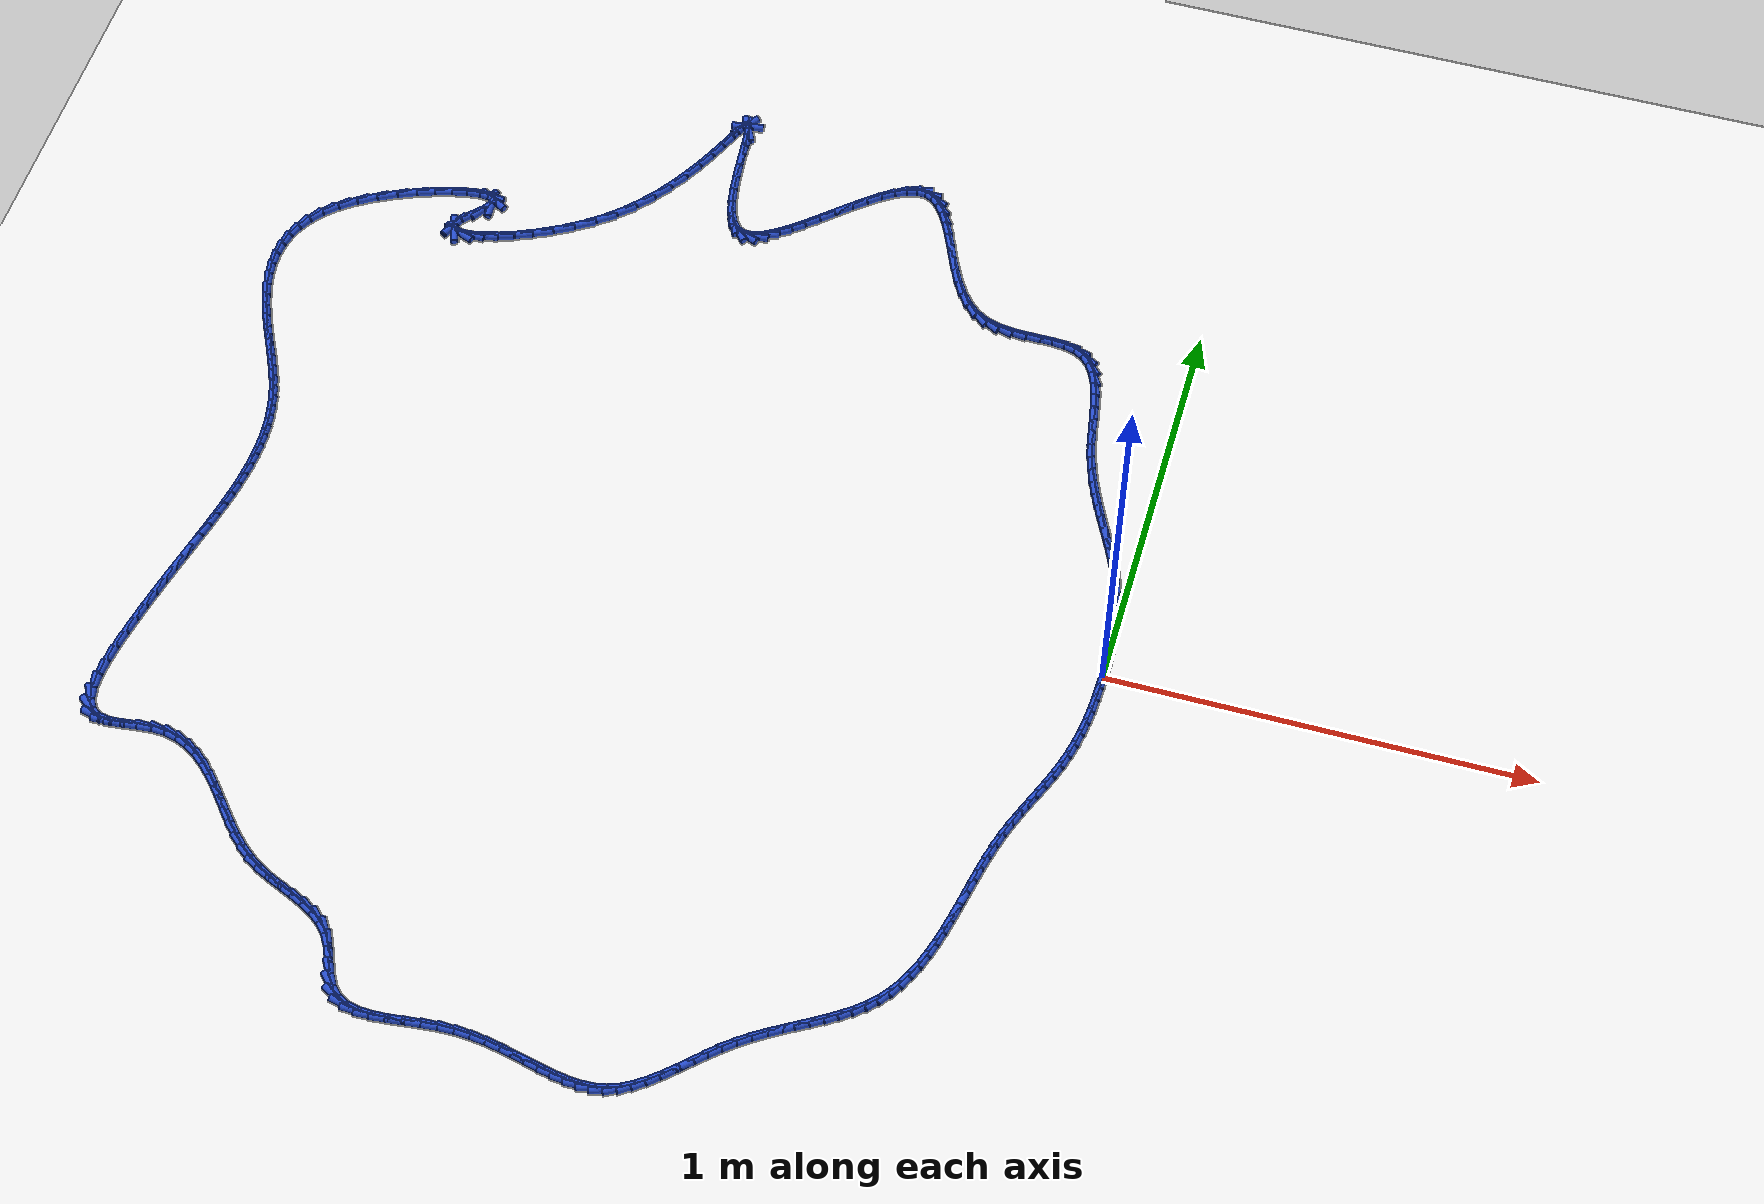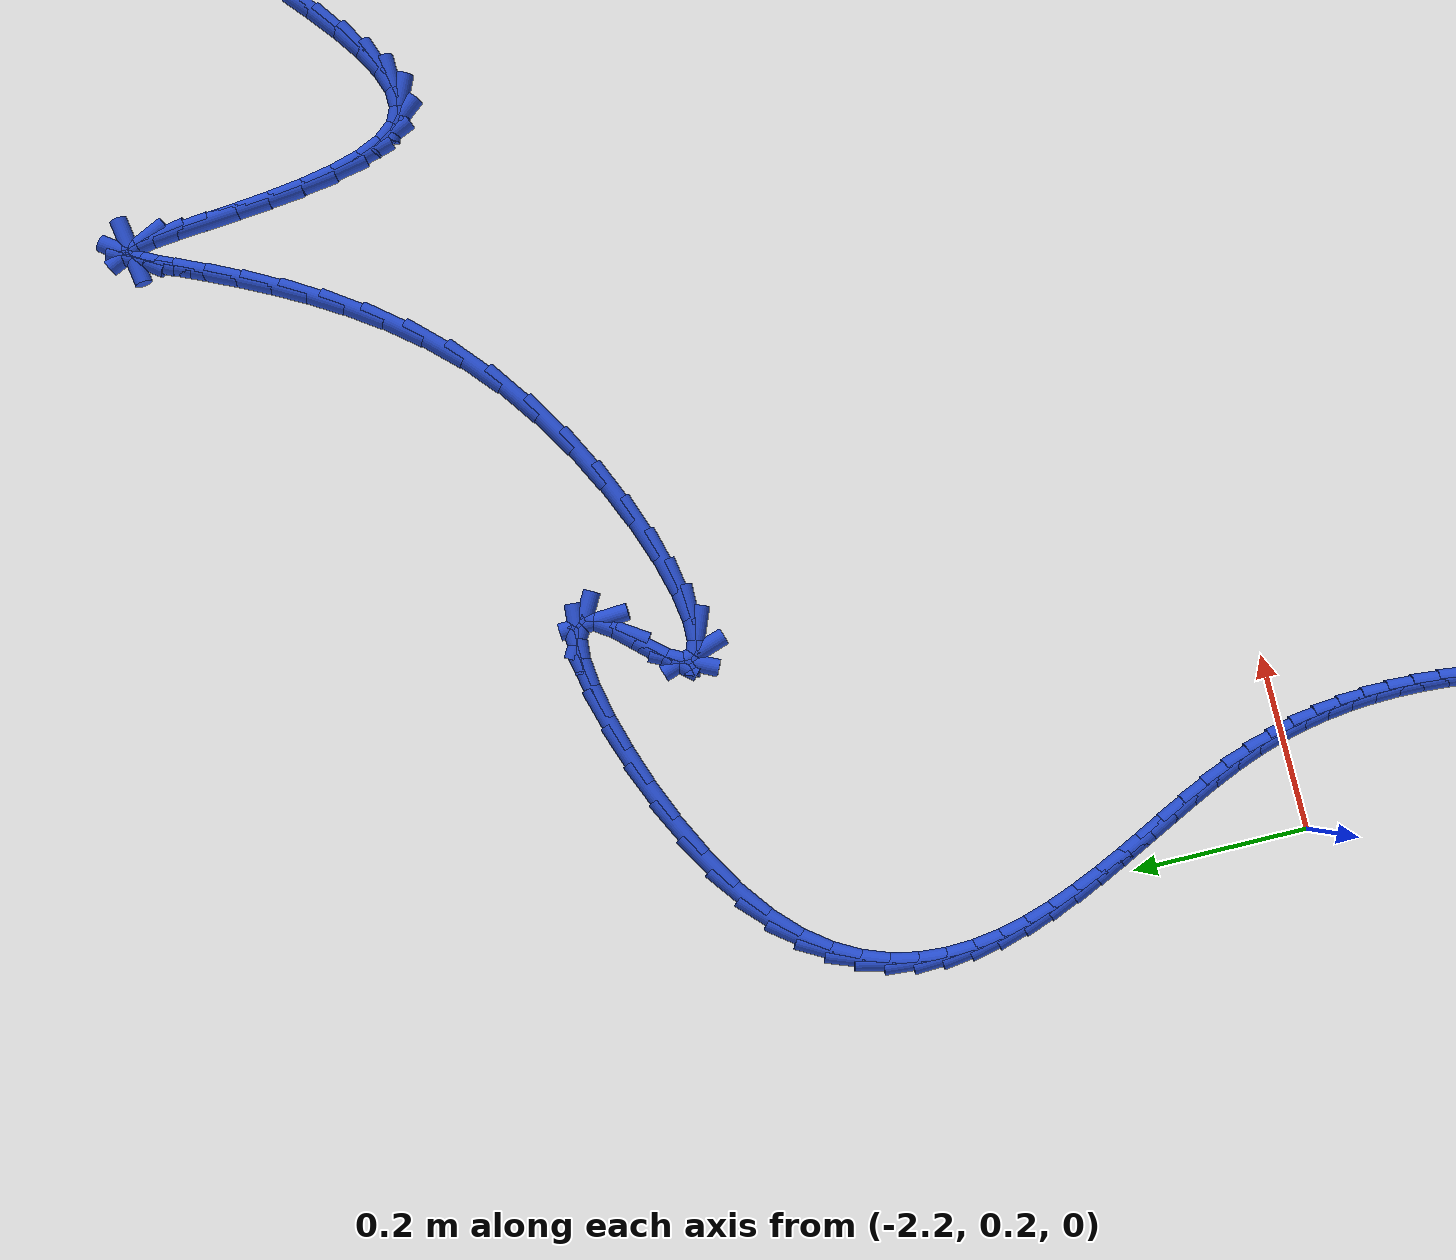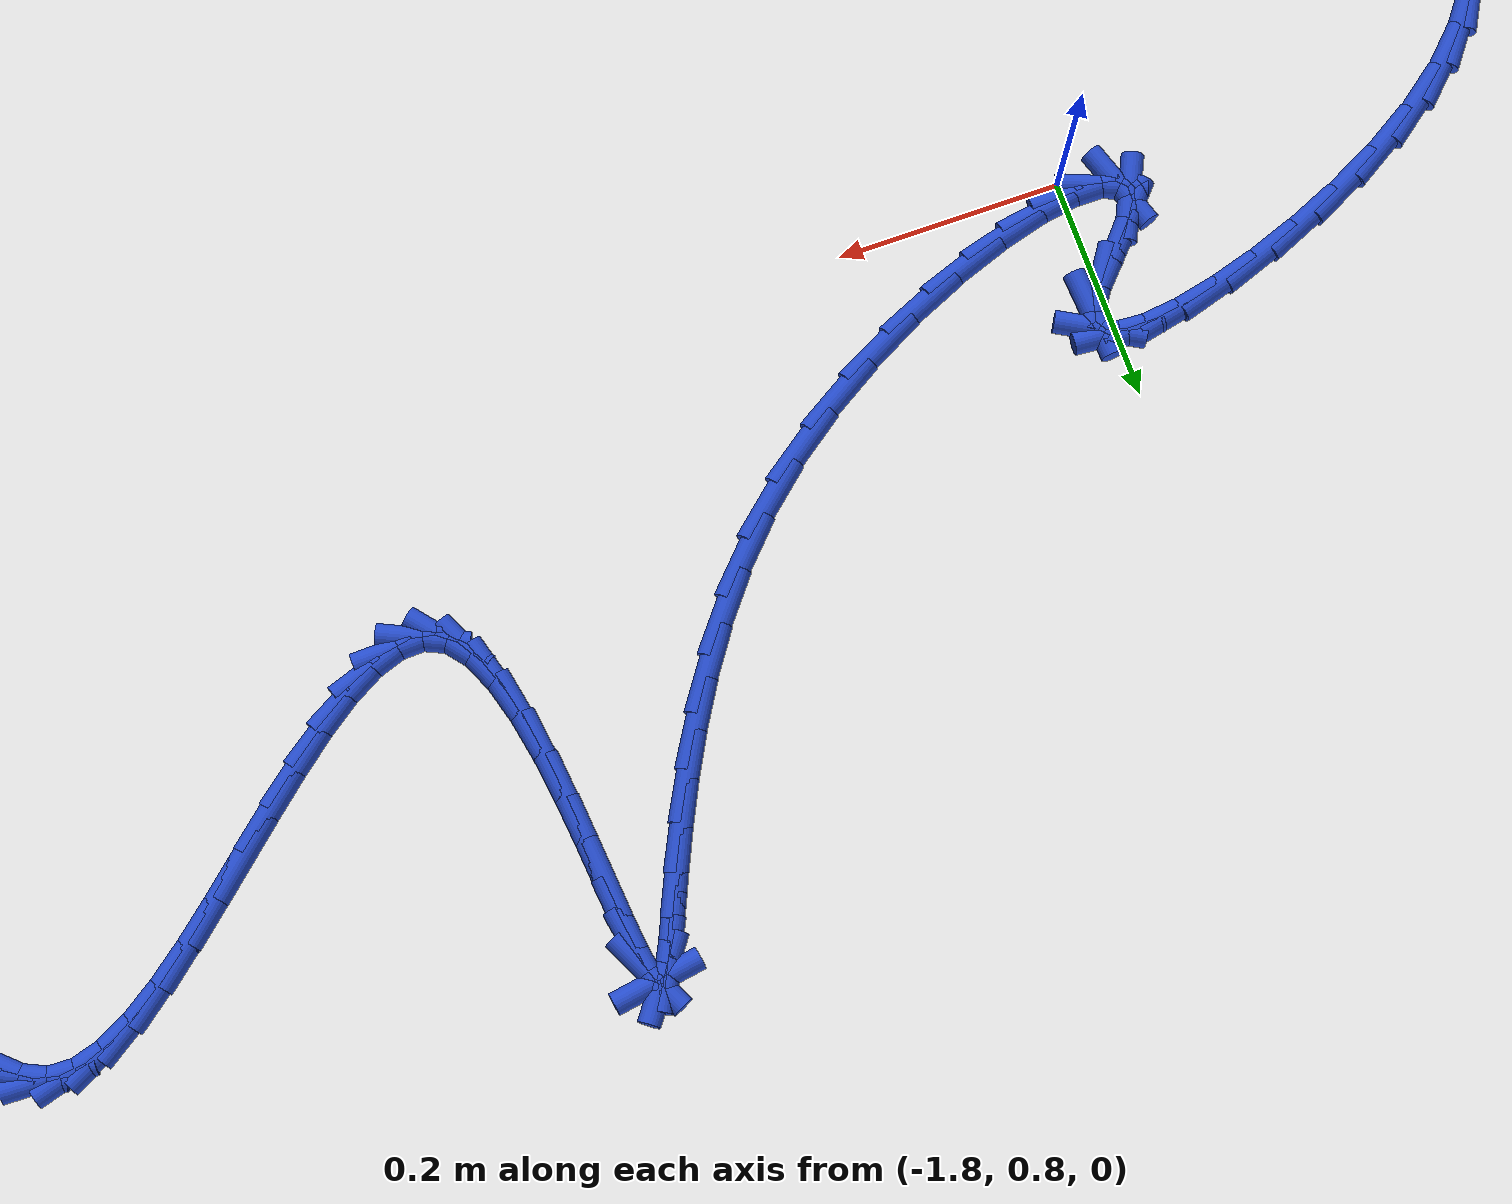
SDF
<sdf version="1.6">
 <world name="default">
  <light name="sun" type="directional">
   <pose>0 0 10 0 -0 0</pose>
   <diffuse>0.8 0.8 0.8 1</diffuse>
   <specular>0.2 0.2 0.2 1</specular>
   <attenuation>
    <range>1000</range>
    <constant>0.9</constant>
    <linear>0.01</linear>
    <quadratic>0.001</quadratic>
   </attenuation>
   <direction>-0.5 0.1 -0.9</direction>
  </light>
  <model name="ground_plane">
   <static>1</static>
   <link name="link">
    <collision name="collision">
     <geometry><plane><normal>0 0 1</normal><size>100 100</size></plane></geometry>
     <surface><friction><ode><mu>100</mu><mu2>50</mu2></ode></friction></surface>
    </collision>
    <visual name="visual">
     <cast_shadows>0</cast_shadows>
     <geometry><plane><normal>0 0 1</normal><size>100 100</size></plane></geometry>
     <material>
      <script><uri>file://media/materials/scripts/gazebo.material</uri><name>Gazebo/WhiteGlow</name></script>
     </material>
    </visual>
   </link>
  </model>
  <gravity>0 0 -9.8</gravity>
  <magnetic_field>6e-06 2.3e-05 -4.2e-05</magnetic_field>
  <atmosphere type="adiabatic"/>
  <physics name="default_physics" default="0" type="ode">
   <max_step_size>0.001</max_step_size>
   <real_time_factor>1</real_time_factor>
   <real_time_update_rate>1000</real_time_update_rate>
  </physics>
  <scene><ambient>0.4 0.4 0.4 1</ambient><background>0.7 0.7 0.7 1</background><shadows>1</shadows></scene>
  <spherical_coordinates>
   <surface_model>EARTH_WGS84</surface_model>
   <latitude_deg>0</latitude_deg>
   <longitude_deg>0</longitude_deg>
   <elevation>0</elevation>
   <heading_deg>0</heading_deg>
  </spherical_coordinates>
  <model name="line">
   <link name="link_0">
    <pose>-1.9949319973733282e-17 -6.938893903907228e-18 0.01 0 1.57 -1.559420882851441</pose>
    <collision name="collision">
     <geometry><cylinder><radius>0.01</radius><length>0.08</length></cylinder></geometry>
    </collision>
    <visual name="visual">
     <material>
      <script><name>Gazebo/Blue</name><uri>file://media/materials/scripts/gazebo.material</uri></script>
     </material>
     <geometry><cylinder><radius>0.01</radius><length>0.08</length></cylinder></geometry>
    </visual>
   </link>
   <link name="link_1">
    <pose>-0.0003757697735197064 0.033031991274708815 0.01 0 1.57 -1.5334565466409051</pose>
    <collision name="collision">
     <geometry><cylinder><radius>0.01</radius><length>0.08</length></cylinder></geometry>
    </collision>
    <visual name="visual">
     <material>
      <script><name>Gazebo/Blue</name><uri>file://media/materials/scripts/gazebo.material</uri></script>
     </material>
     <geometry><cylinder><radius>0.01</radius><length>0.08</length></cylinder></geometry>
    </visual>
   </link>
   <link name="link_2">
    <pose>-0.0016078858074410516 0.06601406417152815 0.01 0 1.57 -1.503292751838299</pose>
    <collision name="collision">
     <geometry><cylinder><radius>0.01</radius><length>0.08</length></cylinder></geometry>
    </collision>
    <visual name="visual">
     <material>
      <script><name>Gazebo/Blue</name><uri>file://media/materials/scripts/gazebo.material</uri></script>
     </material>
     <geometry><cylinder><radius>0.01</radius><length>0.08</length></cylinder></geometry>
    </visual>
   </link>
   <link name="link_3">
    <pose>-0.003825413582089171 0.09881467547785544 0.01 0 1.57 -1.4685913513282585</pose>
    <collision name="collision">
     <geometry><cylinder><radius>0.01</radius><length>0.08</length></cylinder></geometry>
    </collision>
    <visual name="visual">
     <material>
      <script><name>Gazebo/Blue</name><uri>file://media/materials/scripts/gazebo.material</uri></script>
     </material>
     <geometry><cylinder><radius>0.01</radius><length>0.08</length></cylinder></geometry>
    </visual>
   </link>
   <link name="link_4">
    <pose>-0.0071574185777891885 0.13130228198108806 0.01 0 1.57 -1.4289614217760707</pose>
    <collision name="collision">
     <geometry><cylinder><radius>0.01</radius><length>0.08</length></cylinder></geometry>
    </collision>
    <visual name="visual">
     <material>
      <script><name>Gazebo/Blue</name><uri>file://media/materials/scripts/gazebo.material</uri></script>
     </material>
     <geometry><cylinder><radius>0.01</radius><length>0.08</length></cylinder></geometry>
    </visual>
   </link>
   <link name="link_5">
    <pose>-0.011732966274866218 0.1633453404686234 0.01 0 1.57 -1.3839721285990907</pose>
    <collision name="collision">
     <geometry><cylinder><radius>0.01</radius><length>0.08</length></cylinder></geometry>
    </collision>
    <visual name="visual">
     <material>
      <script><name>Gazebo/Blue</name><uri>file://media/materials/scripts/gazebo.material</uri></script>
     </material>
     <geometry><cylinder><radius>0.01</radius><length>0.08</length></cylinder></geometry>
    </visual>
   </link>
   <link name="link_6">
    <pose>-0.01768112215364538 0.19481230772785882 0.01 0 1.57 -1.3331746888996971</pose>
    <collision name="collision">
     <geometry><cylinder><radius>0.01</radius><length>0.08</length></cylinder></geometry>
    </collision>
    <visual name="visual">
     <material>
      <script><name>Gazebo/Blue</name><uri>file://media/materials/scripts/gazebo.material</uri></script>
     </material>
     <geometry><cylinder><radius>0.01</radius><length>0.08</length></cylinder></geometry>
    </visual>
   </link>
   <link name="link_7">
    <pose>-0.0251309516944518 0.22557164054619178 0.01 0 1.57 -1.2765699733630187</pose>
    <collision name="collision">
     <geometry><cylinder><radius>0.01</radius><length>0.08</length></cylinder></geometry>
    </collision>
    <visual name="visual">
     <material>
      <script><name>Gazebo/Blue</name><uri>file://media/materials/scripts/gazebo.material</uri></script>
     </material>
     <geometry><cylinder><radius>0.01</radius><length>0.08</length></cylinder></geometry>
    </visual>
   </link>
   <link name="link_8">
    <pose>-0.0342002856469406 0.2555013281147541 0.01 0 1.57 -1.2222570456791524</pose>
    <collision name="collision">
     <geometry><cylinder><radius>0.01</radius><length>0.08</length></cylinder></geometry>
    </collision>
    <visual name="visual">
     <material>
      <script><name>Gazebo/Blue</name><uri>file://media/materials/scripts/gazebo.material</uri></script>
     </material>
     <geometry><cylinder><radius>0.01</radius><length>0.08</length></cylinder></geometry>
    </visual>
   </link>
   <link name="link_9">
    <pose>-0.044795380790588236 0.2846588751433571 0.01 0 1.57 -1.1783652020640774</pose>
    <collision name="collision">
     <geometry><cylinder><radius>0.01</radius><length>0.08</length></cylinder></geometry>
    </collision>
    <visual name="visual">
     <material>
      <script><name>Gazebo/Blue</name><uri>file://media/materials/scripts/gazebo.material</uri></script>
     </material>
     <geometry><cylinder><radius>0.01</radius><length>0.08</length></cylinder></geometry>
    </visual>
   </link>
   <link name="link_10">
    <pose>-0.056634065349829045 0.3132616635221846 0.01 0 1.57 -1.1458392550065164</pose>
    <collision name="collision">
     <geometry><cylinder><radius>0.01</radius><length>0.08</length></cylinder></geometry>
    </collision>
    <visual name="visual">
     <material>
      <script><name>Gazebo/Blue</name><uri>file://media/materials/scripts/gazebo.material</uri></script>
     </material>
     <geometry><cylinder><radius>0.01</radius><length>0.08</length></cylinder></geometry>
    </visual>
   </link>
   <link name="link_11">
    <pose>-0.06942758138792399 0.34153266334368415 0.01 0 1.57 -1.1249589839583742</pose>
    <collision name="collision">
     <geometry><cylinder><radius>0.01</radius><length>0.08</length></cylinder></geometry>
    </collision>
    <visual name="visual">
     <material>
      <script><name>Gazebo/Blue</name><uri>file://media/materials/scripts/gazebo.material</uri></script>
     </material>
     <geometry><cylinder><radius>0.01</radius><length>0.08</length></cylinder></geometry>
    </visual>
   </link>
   <link name="link_12">
    <pose>-0.08288717096813407 0.3696948447003036 0.01 0 1.57 -1.1157083366132217</pose>
    <collision name="collision">
     <geometry><cylinder><radius>0.01</radius><length>0.08</length></cylinder></geometry>
    </collision>
    <visual name="visual">
     <material>
      <script><name>Gazebo/Blue</name><uri>file://media/materials/scripts/gazebo.material</uri></script>
     </material>
     <geometry><cylinder><radius>0.01</radius><length>0.08</length></cylinder></geometry>
    </visual>
   </link>
   <link name="link_13">
    <pose>-0.09672407615372024 0.39797117768449086 0.01 0 1.57 -1.117865153257444</pose>
    <collision name="collision">
     <geometry><cylinder><radius>0.01</radius><length>0.08</length></cylinder></geometry>
    </collision>
    <visual name="visual">
     <material>
      <script><name>Gazebo/Blue</name><uri>file://media/materials/scripts/gazebo.material</uri></script>
     </material>
     <geometry><cylinder><radius>0.01</radius><length>0.08</length></cylinder></geometry>
    </visual>
   </link>
   <link name="link_14">
    <pose>-0.11064953900794354 0.42658463238869343 0.01 0 1.57 -1.1310509919139706</pose>
    <collision name="collision">
     <geometry><cylinder><radius>0.01</radius><length>0.08</length></cylinder></geometry>
    </collision>
    <visual name="visual">
     <material>
      <script><name>Gazebo/Blue</name><uri>file://media/materials/scripts/gazebo.material</uri></script>
     </material>
     <geometry><cylinder><radius>0.01</radius><length>0.08</length></cylinder></geometry>
    </visual>
   </link>
   <link name="link_15">
    <pose>-0.12437480159406486 0.4557581789053591 0.01 0 1.57 -1.1547412205188685</pose>
    <collision name="collision">
     <geometry><cylinder><radius>0.01</radius><length>0.08</length></cylinder></geometry>
    </collision>
    <visual name="visual">
     <material>
      <script><name>Gazebo/Blue</name><uri>file://media/materials/scripts/gazebo.material</uri></script>
     </material>
     <geometry><cylinder><radius>0.01</radius><length>0.08</length></cylinder></geometry>
    </visual>
   </link>
   <link name="link_16">
    <pose>-0.13761110597534526 0.4857147873269357 0.01 0 1.57 -1.1882443308466029</pose>
    <collision name="collision">
     <geometry><cylinder><radius>0.01</radius><length>0.08</length></cylinder></geometry>
    </collision>
    <visual name="visual">
     <material>
      <script><name>Gazebo/Blue</name><uri>file://media/materials/scripts/gazebo.material</uri></script>
     </material>
     <geometry><cylinder><radius>0.01</radius><length>0.08</length></cylinder></geometry>
    </visual>
   </link>
   <link name="link_17">
    <pose>-0.15006969421504573 0.516677427745871 0.01 0 1.57 -1.23066538115593</pose>
    <collision name="collision">
     <geometry><cylinder><radius>0.01</radius><length>0.08</length></cylinder></geometry>
    </collision>
    <visual name="visual">
     <material>
      <script><name>Gazebo/Blue</name><uri>file://media/materials/scripts/gazebo.material</uri></script>
     </material>
     <geometry><cylinder><radius>0.01</radius><length>0.08</length></cylinder></geometry>
    </visual>
   </link>
   <link name="link_18">
    <pose>-0.16146180837642718 0.5488690702546125 0.01 0 1.57 -1.280872821325462</pose>
    <collision name="collision">
     <geometry><cylinder><radius>0.01</radius><length>0.08</length></cylinder></geometry>
    </collision>
    <visual name="visual">
     <material>
      <script><name>Gazebo/Blue</name><uri>file://media/materials/scripts/gazebo.material</uri></script>
     </material>
     <geometry><cylinder><radius>0.01</radius><length>0.08</length></cylinder></geometry>
    </visual>
   </link>
   <link name="link_19">
    <pose>-0.17149869052275074 0.5825126849456084 0.01 0 1.57 -1.3368128893181541</pose>
    <collision name="collision">
     <geometry><cylinder><radius>0.01</radius><length>0.08</length></cylinder></geometry>
    </collision>
    <visual name="visual">
     <material>
      <script><name>Gazebo/Blue</name><uri>file://media/materials/scripts/gazebo.material</uri></script>
     </material>
     <geometry><cylinder><radius>0.01</radius><length>0.08</length></cylinder></geometry>
    </visual>
   </link>
   <link name="link_20">
    <pose>-0.1799115522170279 0.6178090660223318 0.01 0 1.57 -1.3813441241194686</pose>
    <collision name="collision">
     <geometry><cylinder><radius>0.01</radius><length>0.08</length></cylinder></geometry>
    </collision>
    <visual name="visual">
     <material>
      <script><name>Gazebo/Blue</name><uri>file://media/materials/scripts/gazebo.material</uri></script>
     </material>
     <geometry><cylinder><radius>0.01</radius><length>0.08</length></cylinder></geometry>
    </visual>
   </link>
   <link name="link_21">
    <pose>-0.18692917106644502 0.654406466588551 0.01 0 1.57 -1.4001421490445232</pose>
    <collision name="collision">
     <geometry><cylinder><radius>0.01</radius><length>0.08</length></cylinder></geometry>
    </collision>
    <visual name="visual">
     <material>
      <script><name>Gazebo/Blue</name><uri>file://media/materials/scripts/gazebo.material</uri></script>
     </material>
     <geometry><cylinder><radius>0.01</radius><length>0.08</length></cylinder></geometry>
    </visual>
   </link>
   <link name="link_22">
    <pose>-0.1933001274038336 0.6913759050813586 0.01 0 1.57 -1.3940900047952003</pose>
    <collision name="collision">
     <geometry><cylinder><radius>0.01</radius><length>0.08</length></cylinder></geometry>
    </collision>
    <visual name="visual">
     <material>
      <script><name>Gazebo/Blue</name><uri>file://media/materials/scripts/gazebo.material</uri></script>
     </material>
     <geometry><cylinder><radius>0.01</radius><length>0.08</length></cylinder></geometry>
    </visual>
   </link>
   <link name="link_23">
    <pose>-0.19979742106321252 0.7277612823758701 0.01 0 1.57 -1.3616300016028433</pose>
    <collision name="collision">
     <geometry><cylinder><radius>0.01</radius><length>0.08</length></cylinder></geometry>
    </collision>
    <visual name="visual">
     <material>
      <script><name>Gazebo/Blue</name><uri>file://media/materials/scripts/gazebo.material</uri></script>
     </material>
     <geometry><cylinder><radius>0.01</radius><length>0.08</length></cylinder></geometry>
    </visual>
   </link>
   <link name="link_24">
    <pose>-0.207194051878601 0.7626064993472014 0.01 0 1.57 -1.2974648877573172</pose>
    <collision name="collision">
     <geometry><cylinder><radius>0.01</radius><length>0.08</length></cylinder></geometry>
    </collision>
    <visual name="visual">
     <material>
      <script><name>Gazebo/Blue</name><uri>file://media/materials/scripts/gazebo.material</uri></script>
     </material>
     <geometry><cylinder><radius>0.01</radius><length>0.08</length></cylinder></geometry>
    </visual>
   </link>
   <link name="link_25">
    <pose>-0.21626301968401798 0.7949554568704682 0.01 0 1.57 -1.1916132885952049</pose>
    <collision name="collision">
     <geometry><cylinder><radius>0.01</radius><length>0.08</length></cylinder></geometry>
    </collision>
    <visual name="visual">
     <material>
      <script><name>Gazebo/Blue</name><uri>file://media/materials/scripts/gazebo.material</uri></script>
     </material>
     <geometry><cylinder><radius>0.01</radius><length>0.08</length></cylinder></geometry>
    </visual>
   </link>
   <link name="link_26">
    <pose>-0.22777732431348252 0.8238520558207857 0.01 0 1.57 -1.0291839303407309</pose>
    <collision name="collision">
     <geometry><cylinder><radius>0.01</radius><length>0.08</length></cylinder></geometry>
    </collision>
    <visual name="visual">
     <material>
      <script><name>Gazebo/Blue</name><uri>file://media/materials/scripts/gazebo.material</uri></script>
     </material>
     <geometry><cylinder><radius>0.01</radius><length>0.08</length></cylinder></geometry>
    </visual>
   </link>
   <link name="link_27">
    <pose>-0.24250996560101373 0.8483401970732701 0.01 0 1.57 -0.7959560904787552</pose>
    <collision name="collision">
     <geometry><cylinder><radius>0.01</radius><length>0.08</length></cylinder></geometry>
    </collision>
    <visual name="visual">
     <material>
      <script><name>Gazebo/Blue</name><uri>file://media/materials/scripts/gazebo.material</uri></script>
     </material>
     <geometry><cylinder><radius>0.01</radius><length>0.08</length></cylinder></geometry>
    </visual>
   </link>
   <link name="link_28">
    <pose>-0.2612339433806306 0.8674637815030369 0.01 0 1.57 -0.5015162175015697</pose>
    <collision name="collision">
     <geometry><cylinder><radius>0.01</radius><length>0.08</length></cylinder></geometry>
    </collision>
    <visual name="visual">
     <material>
      <script><name>Gazebo/Blue</name><uri>file://media/materials/scripts/gazebo.material</uri></script>
     </material>
     <geometry><cylinder><radius>0.01</radius><length>0.08</length></cylinder></geometry>
    </visual>
   </link>
   <link name="link_29">
    <pose>-0.28468452212913153 0.8803210971617492 0.01 0 1.57 -0.24486192757231562</pose>
    <collision name="collision">
     <geometry><cylinder><radius>0.01</radius><length>0.08</length></cylinder></geometry>
    </collision>
    <visual name="visual">
     <material>
      <script><name>Gazebo/Blue</name><uri>file://media/materials/scripts/gazebo.material</uri></script>
     </material>
     <geometry><cylinder><radius>0.01</radius><length>0.08</length></cylinder></geometry>
    </visual>
   </link>
   <link name="link_30">
    <pose>-0.3126891901480948 0.8873187908061111 0.01 0 1.57 -0.09148593844415343</pose>
    <collision name="collision">
     <geometry><cylinder><radius>0.01</radius><length>0.08</length></cylinder></geometry>
    </collision>
    <visual name="visual">
     <material>
      <script><name>Gazebo/Blue</name><uri>file://media/materials/scripts/gazebo.material</uri></script>
     </material>
     <geometry><cylinder><radius>0.01</radius><length>0.08</length></cylinder></geometry>
    </visual>
   </link>
   <link name="link_31">
    <pose>-0.344144945165766 0.8902046056820369 0.01 0 1.57 -0.0172550529744351</pose>
    <collision name="collision">
     <geometry><cylinder><radius>0.01</radius><length>0.08</length></cylinder></geometry>
    </collision>
    <visual name="visual">
     <material>
      <script><name>Gazebo/Blue</name><uri>file://media/materials/scripts/gazebo.material</uri></script>
     </material>
     <geometry><cylinder><radius>0.01</radius><length>0.08</length></cylinder></geometry>
    </visual>
   </link>
   <link name="link_32">
    <pose>-0.3779065058037037 0.8907872210225112 0.01 0 1.57 -0.0025226114490034092</pose>
    <collision name="collision">
     <geometry><cylinder><radius>0.01</radius><length>0.08</length></cylinder></geometry>
    </collision>
    <visual name="visual">
     <material>
      <script><name>Gazebo/Blue</name><uri>file://media/materials/scripts/gazebo.material</uri></script>
     </material>
     <geometry><cylinder><radius>0.01</radius><length>0.08</length></cylinder></geometry>
    </visual>
   </link>
   <link name="link_33">
    <pose>-0.4128285906834664 0.8908753160605183 0.01 0 1.57 -0.0401147372451347</pose>
    <collision name="collision">
     <geometry><cylinder><radius>0.01</radius><length>0.08</length></cylinder></geometry>
    </collision>
    <visual name="visual">
     <material>
      <script><name>Gazebo/Blue</name><uri>file://media/materials/scripts/gazebo.material</uri></script>
     </material>
     <geometry><cylinder><radius>0.01</radius><length>0.08</length></cylinder></geometry>
    </visual>
   </link>
   <link name="link_34">
    <pose>-0.4477659184266132 0.8922775700290428 0.01 0 1.57 -0.13305874661754688</pose>
    <collision name="collision">
     <geometry><cylinder><radius>0.01</radius><length>0.08</length></cylinder></geometry>
    </collision>
    <visual name="visual">
     <material>
      <script><name>Gazebo/Blue</name><uri>file://media/materials/scripts/gazebo.material</uri></script>
     </material>
     <geometry><cylinder><radius>0.01</radius><length>0.08</length></cylinder></geometry>
    </visual>
   </link>
   <link name="link_35">
    <pose>-0.48157320765470224 0.8968026621610689 0.01 0 1.57 -0.2913700513080233</pose>
    <collision name="collision">
     <geometry><cylinder><radius>0.01</radius><length>0.08</length></cylinder></geometry>
    </collision>
    <visual name="visual">
     <material>
      <script><name>Gazebo/Blue</name><uri>file://media/materials/scripts/gazebo.material</uri></script>
     </material>
     <geometry><cylinder><radius>0.01</radius><length>0.08</length></cylinder></geometry>
    </visual>
   </link>
   <link name="link_36">
    <pose>-0.513105176989292 0.9062592716895809 0.01 0 1.57 -0.5166177321962132</pose>
    <collision name="collision">
     <geometry><cylinder><radius>0.01</radius><length>0.08</length></cylinder></geometry>
    </collision>
    <visual name="visual">
     <material>
      <script><name>Gazebo/Blue</name><uri>file://media/materials/scripts/gazebo.material</uri></script>
     </material>
     <geometry><cylinder><radius>0.01</radius><length>0.08</length></cylinder></geometry>
    </visual>
   </link>
   <link name="link_37">
    <pose>-0.5413101616347828 0.922281943203062 0.01 0 1.57 -0.7348717533185812</pose>
    <collision name="collision">
     <geometry><cylinder><radius>0.01</radius><length>0.08</length></cylinder></geometry>
    </collision>
    <visual name="visual">
     <material>
      <script><name>Gazebo/Blue</name><uri>file://media/materials/scripts/gazebo.material</uri></script>
     </material>
     <geometry><cylinder><radius>0.01</radius><length>0.08</length></cylinder></geometry>
    </visual>
   </link>
   <link name="link_38">
    <pose>-0.5661100494906615 0.944694332157785 0.01 0 1.57 -0.8993139980327384</pose>
    <collision name="collision">
     <geometry><cylinder><radius>0.01</radius><length>0.08</length></cylinder></geometry>
    </collision>
    <visual name="visual">
     <material>
      <script><name>Gazebo/Blue</name><uri>file://media/materials/scripts/gazebo.material</uri></script>
     </material>
     <geometry><cylinder><radius>0.01</radius><length>0.08</length></cylinder></geometry>
    </visual>
   </link>
   <link name="link_39">
    <pose>-0.5880043153397887 0.9722457342806643 0.01 0 1.57 -1.0155283808442939</pose>
    <collision name="collision">
     <geometry><cylinder><radius>0.01</radius><length>0.08</length></cylinder></geometry>
    </collision>
    <visual name="visual">
     <material>
      <script><name>Gazebo/Blue</name><uri>file://media/materials/scripts/gazebo.material</uri></script>
     </material>
     <geometry><cylinder><radius>0.01</radius><length>0.08</length></cylinder></geometry>
    </visual>
   </link>
   <link name="link_40">
    <pose>-0.6075000258484518 1.0036713237628607 0.01 0 1.57 -1.0934524089914617</pose>
    <collision name="collision">
     <geometry><cylinder><radius>0.01</radius><length>0.08</length></cylinder></geometry>
    </collision>
    <visual name="visual">
     <material>
      <script><name>Gazebo/Blue</name><uri>file://media/materials/scripts/gazebo.material</uri></script>
     </material>
     <geometry><cylinder><radius>0.01</radius><length>0.08</length></cylinder></geometry>
    </visual>
   </link>
   <link name="link_41">
    <pose>-0.6251042476829389 1.0377062747955361 0.01 0 1.57 -1.140935907727501</pose>
    <collision name="collision">
     <geometry><cylinder><radius>0.01</radius><length>0.08</length></cylinder></geometry>
    </collision>
    <visual name="visual">
     <material>
      <script><name>Gazebo/Blue</name><uri>file://media/materials/scripts/gazebo.material</uri></script>
     </material>
     <geometry><cylinder><radius>0.01</radius><length>0.08</length></cylinder></geometry>
    </visual>
   </link>
   <link name="link_42">
    <pose>-0.6413240475095378 1.073085761569852 0.01 0 1.57 -1.1624396435981152</pose>
    <collision name="collision">
     <geometry><cylinder><radius>0.01</radius><length>0.08</length></cylinder></geometry>
    </collision>
    <visual name="visual">
     <material>
      <script><name>Gazebo/Blue</name><uri>file://media/materials/scripts/gazebo.material</uri></script>
     </material>
     <geometry><cylinder><radius>0.01</radius><length>0.08</length></cylinder></geometry>
    </visual>
   </link>
   <link name="link_43">
    <pose>-0.6566664919945361 1.1085449582769695 0.01 0 1.57 -1.1589432614752928</pose>
    <collision name="collision">
     <geometry><cylinder><radius>0.01</radius><length>0.08</length></cylinder></geometry>
    </collision>
    <visual name="visual">
     <material>
      <script><name>Gazebo/Blue</name><uri>file://media/materials/scripts/gazebo.material</uri></script>
     </material>
     <geometry><cylinder><radius>0.01</radius><length>0.08</length></cylinder></geometry>
    </visual>
   </link>
   <link name="link_44">
    <pose>-0.6716386478042213 1.1428190391080502 0.01 0 1.57 -1.1275411217396751</pose>
    <collision name="collision">
     <geometry><cylinder><radius>0.01</radius><length>0.08</length></cylinder></geometry>
    </collision>
    <visual name="visual">
     <material>
      <script><name>Gazebo/Blue</name><uri>file://media/materials/scripts/gazebo.material</uri></script>
     </material>
     <geometry><cylinder><radius>0.01</radius><length>0.08</length></cylinder></geometry>
    </visual>
   </link>
   <link name="link_45">
    <pose>-0.6867475816048817 1.1746431782542555 0.01 0 1.57 -1.059995791432483</pose>
    <collision name="collision">
     <geometry><cylinder><radius>0.01</radius><length>0.08</length></cylinder></geometry>
    </collision>
    <visual name="visual">
     <material>
      <script><name>Gazebo/Blue</name><uri>file://media/materials/scripts/gazebo.material</uri></script>
     </material>
     <geometry><cylinder><radius>0.01</radius><length>0.08</length></cylinder></geometry>
    </visual>
   </link>
   <link name="link_46">
    <pose>-0.7025003600628049 1.2027525499067473 0.01 0 1.57 -0.9396842626617987</pose>
    <collision name="collision">
     <geometry><cylinder><radius>0.01</radius><length>0.08</length></cylinder></geometry>
    </collision>
    <visual name="visual">
     <material>
      <script><name>Gazebo/Blue</name><uri>file://media/materials/scripts/gazebo.material</uri></script>
     </material>
     <geometry><cylinder><radius>0.01</radius><length>0.08</length></cylinder></geometry>
    </visual>
   </link>
   <link name="link_47">
    <pose>-0.7194040498442784 1.2258823282566862 0.01 0 1.57 -0.738142844136037</pose>
    <collision name="collision">
     <geometry><cylinder><radius>0.01</radius><length>0.08</length></cylinder></geometry>
    </collision>
    <visual name="visual">
     <material>
      <script><name>Gazebo/Blue</name><uri>file://media/materials/scripts/gazebo.material</uri></script>
     </material>
     <geometry><cylinder><radius>0.01</radius><length>0.08</length></cylinder></geometry>
    </visual>
   </link>
   <link name="link_48">
    <pose>-0.7379657176155897 1.2427676874952338 0.01 0 1.57 -0.4248219263611786</pose>
    <collision name="collision">
     <geometry><cylinder><radius>0.01</radius><length>0.08</length></cylinder></geometry>
    </collision>
    <visual name="visual">
     <material>
      <script><name>Gazebo/Blue</name><uri>file://media/materials/scripts/gazebo.material</uri></script>
     </material>
     <geometry><cylinder><radius>0.01</radius><length>0.08</length></cylinder></geometry>
    </visual>
   </link>
   <link name="link_49">
    <pose>-0.7586924300430272 1.2521438018135522 0.01 0 1.57 -0.03178304099105054</pose>
    <collision name="collision">
     <geometry><cylinder><radius>0.01</radius><length>0.08</length></cylinder></geometry>
    </collision>
    <visual name="visual">
     <material>
      <script><name>Gazebo/Blue</name><uri>file://media/materials/scripts/gazebo.material</uri></script>
     </material>
     <geometry><cylinder><radius>0.01</radius><length>0.08</length></cylinder></geometry>
    </visual>
   </link>
   <link name="link_50">
    <pose>-0.7820406890772185 1.252886130461662 0.01 0 1.57 0.28170518062247596</pose>
    <collision name="collision">
     <geometry><cylinder><radius>0.01</radius><length>0.08</length></cylinder></geometry>
    </collision>
    <visual name="visual">
     <material>
      <script><name>Gazebo/Blue</name><uri>file://media/materials/scripts/gazebo.material</uri></script>
     </material>
     <geometry><cylinder><radius>0.01</radius><length>0.08</length></cylinder></geometry>
    </visual>
   </link>
   <link name="link_51">
    <pose>-0.8079164106611737 1.2453976601260228 0.01 0 1.57 0.4748050582417541</pose>
    <collision name="collision">
     <geometry><cylinder><radius>0.01</radius><length>0.08</length></cylinder></geometry>
    </collision>
    <visual name="visual">
     <material>
      <script><name>Gazebo/Blue</name><uri>file://media/materials/scripts/gazebo.material</uri></script>
     </material>
     <geometry><cylinder><radius>0.01</radius><length>0.08</length></cylinder></geometry>
    </visual>
   </link>
   <link name="link_52">
    <pose>-0.8358872080690265 1.2310199531222934 0.01 0 1.57 0.5917166206231078</pose>
    <collision name="collision">
     <geometry><cylinder><radius>0.01</radius><length>0.08</length></cylinder></geometry>
    </collision>
    <visual name="visual">
     <material>
      <script><name>Gazebo/Blue</name><uri>file://media/materials/scripts/gazebo.material</uri></script>
     </material>
     <geometry><cylinder><radius>0.01</radius><length>0.08</length></cylinder></geometry>
    </visual>
   </link>
   <link name="link_53">
    <pose>-0.8655157696188389 1.211108235399825 0.01 0 1.57 0.6629958302061411</pose>
    <collision name="collision">
     <geometry><cylinder><radius>0.01</radius><length>0.08</length></cylinder></geometry>
    </collision>
    <visual name="visual">
     <material>
      <script><name>Gazebo/Blue</name><uri>file://media/materials/scripts/gazebo.material</uri></script>
     </material>
     <geometry><cylinder><radius>0.01</radius><length>0.08</length></cylinder></geometry>
    </visual>
   </link>
   <link name="link_54">
    <pose>-0.8963647836286723 1.1870177329079667 0.01 0 1.57 0.7049844362468882</pose>
    <collision name="collision">
     <geometry><cylinder><radius>0.01</radius><length>0.08</length></cylinder></geometry>
    </collision>
    <visual name="visual">
     <material>
      <script><name>Gazebo/Blue</name><uri>file://media/materials/scripts/gazebo.material</uri></script>
     </material>
     <geometry><cylinder><radius>0.01</radius><length>0.08</length></cylinder></geometry>
    </visual>
   </link>
   <link name="link_55">
    <pose>-0.927996938416589 1.1601036715960702 0.01 0 1.57 0.7258997648162204</pose>
    <collision name="collision">
     <geometry><cylinder><radius>0.01</radius><length>0.08</length></cylinder></geometry>
    </collision>
    <visual name="visual">
     <material>
      <script><name>Gazebo/Blue</name><uri>file://media/materials/scripts/gazebo.material</uri></script>
     </material>
     <geometry><cylinder><radius>0.01</radius><length>0.08</length></cylinder></geometry>
    </visual>
   </link>
   <link name="link_56">
    <pose>-0.9599749223006493 1.1317212774134848 0.01 0 1.57 0.7292979697665133</pose>
    <collision name="collision">
     <geometry><cylinder><radius>0.01</radius><length>0.08</length></cylinder></geometry>
    </collision>
    <visual name="visual">
     <material>
      <script><name>Gazebo/Blue</name><uri>file://media/materials/scripts/gazebo.material</uri></script>
     </material>
     <geometry><cylinder><radius>0.01</radius><length>0.08</length></cylinder></geometry>
    </visual>
   </link>
   <link name="link_57">
    <pose>-0.9918614235989159 1.1032257763095612 0.01 0 1.57 0.7154858670351756</pose>
    <collision name="collision">
     <geometry><cylinder><radius>0.01</radius><length>0.08</length></cylinder></geometry>
    </collision>
    <visual name="visual">
     <material>
      <script><name>Gazebo/Blue</name><uri>file://media/materials/scripts/gazebo.material</uri></script>
     </material>
     <geometry><cylinder><radius>0.01</radius><length>0.08</length></cylinder></geometry>
    </visual>
   </link>
   <link name="link_58">
    <pose>-1.0232191306294505 1.0759723942336499 0.01 0 1.57 0.6815800344077225</pose>
    <collision name="collision">
     <geometry><cylinder><radius>0.01</radius><length>0.08</length></cylinder></geometry>
    </collision>
    <visual name="visual">
     <material>
      <script><name>Gazebo/Blue</name><uri>file://media/materials/scripts/gazebo.material</uri></script>
     </material>
     <geometry><cylinder><radius>0.01</radius><length>0.08</length></cylinder></geometry>
    </visual>
   </link>
   <link name="link_59">
    <pose>-1.0536107317103147 1.0513163571351014 0.01 0 1.57 0.6201951381950903</pose>
    <collision name="collision">
     <geometry><cylinder><radius>0.01</radius><length>0.08</length></cylinder></geometry>
    </collision>
    <visual name="visual">
     <material>
      <script><name>Gazebo/Blue</name><uri>file://media/materials/scripts/gazebo.material</uri></script>
     </material>
     <geometry><cylinder><radius>0.01</radius><length>0.08</length></cylinder></geometry>
    </visual>
   </link>
   <link name="link_60">
    <pose>-1.0825989151595696 1.030612890963266 0.01 0 1.57 0.5158866542104761</pose>
    <collision name="collision">
     <geometry><cylinder><radius>0.01</radius><length>0.08</length></cylinder></geometry>
    </collision>
    <visual name="visual">
     <material>
      <script><name>Gazebo/Blue</name><uri>file://media/materials/scripts/gazebo.material</uri></script>
     </material>
     <geometry><cylinder><radius>0.01</radius><length>0.08</length></cylinder></geometry>
    </visual>
   </link>
   <link name="link_61">
    <pose>-1.1097463692952774 1.0152172216674935 0.01 0 1.57 0.33769007486854064</pose>
    <collision name="collision">
     <geometry><cylinder><radius>0.01</radius><length>0.08</length></cylinder></geometry>
    </collision>
    <visual name="visual">
     <material>
      <script><name>Gazebo/Blue</name><uri>file://media/materials/scripts/gazebo.material</uri></script>
     </material>
     <geometry><cylinder><radius>0.01</radius><length>0.08</length></cylinder></geometry>
    </visual>
   </link>
   <link name="link_62">
    <pose>-1.1346157824354997 1.0064845751971345 0.01 0 1.57 0.032235635877049106</pose>
    <collision name="collision">
     <geometry><cylinder><radius>0.01</radius><length>0.08</length></cylinder></geometry>
    </collision>
    <visual name="visual">
     <material>
      <script><name>Gazebo/Blue</name><uri>file://media/materials/scripts/gazebo.material</uri></script>
     </material>
     <geometry><cylinder><radius>0.01</radius><length>0.08</length></cylinder></geometry>
    </visual>
   </link>
   <link name="link_63">
    <pose>-1.156769842898298 1.0057701775015397 0.01 0 1.57 -0.42759001840637256</pose>
    <collision name="collision">
     <geometry><cylinder><radius>0.01</radius><length>0.08</length></cylinder></geometry>
    </collision>
    <visual name="visual">
     <material>
      <script><name>Gazebo/Blue</name><uri>file://media/materials/scripts/gazebo.material</uri></script>
     </material>
     <geometry><cylinder><radius>0.01</radius><length>0.08</length></cylinder></geometry>
    </visual>
   </link>
   <link name="link_64">
    <pose>-1.1757712392341662 1.0144292536124595 0.01 0 1.57 -0.8789164556793228</pose>
    <collision name="collision">
     <geometry><cylinder><radius>0.01</radius><length>0.08</length></cylinder></geometry>
    </collision>
    <visual name="visual">
     <material>
      <script><name>Gazebo/Blue</name><uri>file://media/materials/scripts/gazebo.material</uri></script>
     </material>
     <geometry><cylinder><radius>0.01</radius><length>0.08</length></cylinder></geometry>
    </visual>
   </link>
   <link name="link_65">
    <pose>-1.1913351798251317 1.0332149070739096 0.01 0 1.57 -1.1440539094973783</pose>
    <collision name="collision">
     <geometry><cylinder><radius>0.01</radius><length>0.08</length></cylinder></geometry>
    </collision>
    <visual name="visual">
     <material>
      <script><name>Gazebo/Blue</name><uri>file://media/materials/scripts/gazebo.material</uri></script>
     </material>
     <geometry><cylinder><radius>0.01</radius><length>0.08</length></cylinder></geometry>
    </visual>
   </link>
   <link name="link_66">
    <pose>-1.2037660164721011 1.0605544067610935 0.01 0 1.57 -1.2897915619573241</pose>
    <collision name="collision">
     <geometry><cylinder><radius>0.01</radius><length>0.08</length></cylinder></geometry>
    </collision>
    <visual name="visual">
     <material>
      <script><name>Gazebo/Blue</name><uri>file://media/materials/scripts/gazebo.material</uri></script>
     </material>
     <geometry><cylinder><radius>0.01</radius><length>0.08</length></cylinder></geometry>
    </visual>
   </link>
   <link name="link_67">
    <pose>-1.2135103312649558 1.094313521367006 0.01 0 1.57 -1.3760439174068004</pose>
    <collision name="collision">
     <geometry><cylinder><radius>0.01</radius><length>0.08</length></cylinder></geometry>
    </collision>
    <visual name="visual">
     <material>
      <script><name>Gazebo/Blue</name><uri>file://media/materials/scripts/gazebo.material</uri></script>
     </material>
     <geometry><cylinder><radius>0.01</radius><length>0.08</length></cylinder></geometry>
    </visual>
   </link>
   <link name="link_68">
    <pose>-1.2210147062935743 1.1323580195846408 0.01 0 1.57 -1.42966048358006</pose>
    <collision name="collision">
     <geometry><cylinder><radius>0.01</radius><length>0.08</length></cylinder></geometry>
    </collision>
    <visual name="visual">
     <material>
      <script><name>Gazebo/Blue</name><uri>file://media/materials/scripts/gazebo.material</uri></script>
     </material>
     <geometry><cylinder><radius>0.01</radius><length>0.08</length></cylinder></geometry>
    </visual>
   </link>
   <link name="link_69">
    <pose>-1.2267257236478364 1.1725536701069914 0.01 0 1.57 -1.4626901601008142</pose>
    <collision name="collision">
     <geometry><cylinder><radius>0.01</radius><length>0.08</length></cylinder></geometry>
    </collision>
    <visual name="visual">
     <material>
      <script><name>Gazebo/Blue</name><uri>file://media/materials/scripts/gazebo.material</uri></script>
     </material>
     <geometry><cylinder><radius>0.01</radius><length>0.08</length></cylinder></geometry>
    </visual>
   </link>
   <link name="link_70">
    <pose>-1.2310899654176226 1.2127662416270535 0.01 0 1.57 -1.4801144998195659</pose>
    <collision name="collision">
     <geometry><cylinder><radius>0.01</radius><length>0.08</length></cylinder></geometry>
    </collision>
    <visual name="visual">
     <material>
      <script><name>Gazebo/Blue</name><uri>file://media/materials/scripts/gazebo.material</uri></script>
     </material>
     <geometry><cylinder><radius>0.01</radius><length>0.08</length></cylinder></geometry>
    </visual>
   </link>
   <link name="link_71">
    <pose>-1.2345540136928124 1.2508615028378198 0.01 0 1.57 -1.4820786988495482</pose>
    <collision name="collision">
     <geometry><cylinder><radius>0.01</radius><length>0.08</length></cylinder></geometry>
    </collision>
    <visual name="visual">
     <material>
      <script><name>Gazebo/Blue</name><uri>file://media/materials/scripts/gazebo.material</uri></script>
     </material>
     <geometry><cylinder><radius>0.01</radius><length>0.08</length></cylinder></geometry>
    </visual>
   </link>
   <link name="link_72">
    <pose>-1.237564450563285 1.284705222432285 0.01 0 1.57 -1.4618473650053017</pose>
    <collision name="collision">
     <geometry><cylinder><radius>0.01</radius><length>0.08</length></cylinder></geometry>
    </collision>
    <visual name="visual">
     <material>
      <script><name>Gazebo/Blue</name><uri>file://media/materials/scripts/gazebo.material</uri></script>
     </material>
     <geometry><cylinder><radius>0.01</radius><length>0.08</length></cylinder></geometry>
    </visual>
   </link>
   <link name="link_73">
    <pose>-1.240567858118921 1.3121631691034437 0.01 0 1.57 -1.3909582600576658</pose>
    <collision name="collision">
     <geometry><cylinder><radius>0.01</radius><length>0.08</length></cylinder></geometry>
    </collision>
    <visual name="visual">
     <material>
      <script><name>Gazebo/Blue</name><uri>file://media/materials/scripts/gazebo.material</uri></script>
     </material>
     <geometry><cylinder><radius>0.01</radius><length>0.08</length></cylinder></geometry>
    </visual>
   </link>
   <link name="link_74">
    <pose>-1.2440108184495997 1.3311011115442895 0.01 0 1.57 -1.1150318749708443</pose>
    <collision name="collision">
     <geometry><cylinder><radius>0.01</radius><length>0.08</length></cylinder></geometry>
    </collision>
    <visual name="visual">
     <material>
      <script><name>Gazebo/Blue</name><uri>file://media/materials/scripts/gazebo.material</uri></script>
     </material>
     <geometry><cylinder><radius>0.01</radius><length>0.08</length></cylinder></geometry>
    </visual>
   </link>
   <link name="link_75">
    <pose>-1.2483133444187737 1.339878471151186 0.01 0 1.57 0.1642797061229624</pose>
    <collision name="collision">
     <geometry><cylinder><radius>0.01</radius><length>0.08</length></cylinder></geometry>
    </collision>
    <visual name="visual">
     <material>
      <script><name>Gazebo/Blue</name><uri>file://media/materials/scripts/gazebo.material</uri></script>
     </material>
     <geometry><cylinder><radius>0.01</radius><length>0.08</length></cylinder></geometry>
    </visual>
   </link>
   <link name="link_76">
    <pose>-1.2537814907538192 1.3389719963755173 0.01 0 1.57 0.9442838127265565</pose>
    <collision name="collision">
     <geometry><cylinder><radius>0.01</radius><length>0.08</length></cylinder></geometry>
    </collision>
    <visual name="visual">
     <material>
      <script><name>Gazebo/Blue</name><uri>file://media/materials/scripts/gazebo.material</uri></script>
     </material>
     <geometry><cylinder><radius>0.01</radius><length>0.08</length></cylinder></geometry>
    </visual>
   </link>
   <link name="link_77">
    <pose>-1.260690765553075 1.3294259879850352 0.01 0 1.57 1.1045714313756598</pose>
    <collision name="collision">
     <geometry><cylinder><radius>0.01</radius><length>0.08</length></cylinder></geometry>
    </collision>
    <visual name="visual">
     <material>
      <script><name>Gazebo/Blue</name><uri>file://media/materials/scripts/gazebo.material</uri></script>
     </material>
     <geometry><cylinder><radius>0.01</radius><length>0.08</length></cylinder></geometry>
    </visual>
   </link>
   <link name="link_78">
    <pose>-1.2693166765563606 1.3122847534087323 0.01 0 1.57 1.1494672898475495</pose>
    <collision name="collision">
     <geometry><cylinder><radius>0.01</radius><length>0.08</length></cylinder></geometry>
    </collision>
    <visual name="visual">
     <material>
      <script><name>Gazebo/Blue</name><uri>file://media/materials/scripts/gazebo.material</uri></script>
     </material>
     <geometry><cylinder><radius>0.01</radius><length>0.08</length></cylinder></geometry>
    </visual>
   </link>
   <link name="link_79">
    <pose>-1.2799347315034961 1.288592600075601 0.01 0 1.57 1.155192468071799</pose>
    <collision name="collision">
     <geometry><cylinder><radius>0.01</radius><length>0.08</length></cylinder></geometry>
    </collision>
    <visual name="visual">
     <material>
      <script><name>Gazebo/Blue</name><uri>file://media/materials/scripts/gazebo.material</uri></script>
     </material>
     <geometry><cylinder><radius>0.01</radius><length>0.08</length></cylinder></geometry>
    </visual>
   </link>
   <link name="link_80">
    <pose>-1.2928204381343014 1.2593938354146341 0.01 0 1.57 1.141012534290716</pose>
    <collision name="collision">
     <geometry><cylinder><radius>0.01</radius><length>0.08</length></cylinder></geometry>
    </collision>
    <visual name="visual">
     <material>
      <script><name>Gazebo/Blue</name><uri>file://media/materials/scripts/gazebo.material</uri></script>
     </material>
     <geometry><cylinder><radius>0.01</radius><length>0.08</length></cylinder></geometry>
    </visual>
   </link>
   <link name="link_81">
    <pose>-1.3082493041885956 1.225732766854823 0.01 0 1.57 1.1134685774069717</pose>
    <collision name="collision">
     <geometry><cylinder><radius>0.01</radius><length>0.08</length></cylinder></geometry>
    </collision>
    <visual name="visual">
     <material>
      <script><name>Gazebo/Blue</name><uri>file://media/materials/scripts/gazebo.material</uri></script>
     </material>
     <geometry><cylinder><radius>0.01</radius><length>0.08</length></cylinder></geometry>
    </visual>
   </link>
   <link name="link_82">
    <pose>-1.326496837406199 1.1886537018251606 0.01 0 1.57 1.0749329161192567</pose>
    <collision name="collision">
     <geometry><cylinder><radius>0.01</radius><length>0.08</length></cylinder></geometry>
    </collision>
    <visual name="visual">
     <material>
      <script><name>Gazebo/Blue</name><uri>file://media/materials/scripts/gazebo.material</uri></script>
     </material>
     <geometry><cylinder><radius>0.01</radius><length>0.08</length></cylinder></geometry>
    </visual>
   </link>
   <link name="link_83">
    <pose>-1.3478385455269317 1.1492009477546388 0.01 0 1.57 1.026023071655415</pose>
    <collision name="collision">
     <geometry><cylinder><radius>0.01</radius><length>0.08</length></cylinder></geometry>
    </collision>
    <visual name="visual">
     <material>
      <script><name>Gazebo/Blue</name><uri>file://media/materials/scripts/gazebo.material</uri></script>
     </material>
     <geometry><cylinder><radius>0.01</radius><length>0.08</length></cylinder></geometry>
    </visual>
   </link>
   <link name="link_84">
    <pose>-1.3725499362906126 1.108418812072251 0.01 0 1.57 0.9664800934651094</pose>
    <collision name="collision">
     <geometry><cylinder><radius>0.01</radius><length>0.08</length></cylinder></geometry>
    </collision>
    <visual name="visual">
     <material>
      <script><name>Gazebo/Blue</name><uri>file://media/materials/scripts/gazebo.material</uri></script>
     </material>
     <geometry><cylinder><radius>0.01</radius><length>0.08</length></cylinder></geometry>
    </visual>
   </link>
   <link name="link_85">
    <pose>-1.4009065174370618 1.0673516022069884 0.01 0 1.57 0.8955881523786361</pose>
    <collision name="collision">
     <geometry><cylinder><radius>0.01</radius><length>0.08</length></cylinder></geometry>
    </collision>
    <visual name="visual">
     <material>
      <script><name>Gazebo/Blue</name><uri>file://media/materials/scripts/gazebo.material</uri></script>
     </material>
     <geometry><cylinder><radius>0.01</radius><length>0.08</length></cylinder></geometry>
    </visual>
   </link>
   <link name="link_86">
    <pose>-1.4331837967060996 1.0270436255878435 0.01 0 1.57 0.8124788597372141</pose>
    <collision name="collision">
     <geometry><cylinder><radius>0.01</radius><length>0.08</length></cylinder></geometry>
    </collision>
    <visual name="visual">
     <material>
      <script><name>Gazebo/Blue</name><uri>file://media/materials/scripts/gazebo.material</uri></script>
     </material>
     <geometry><cylinder><radius>0.01</radius><length>0.08</length></cylinder></geometry>
    </visual>
   </link>
   <link name="link_87">
    <pose>-1.4696572818375453 0.9885391896438097 0.01 0 1.57 0.717372114097598</pose>
    <collision name="collision">
     <geometry><cylinder><radius>0.01</radius><length>0.08</length></cylinder></geometry>
    </collision>
    <visual name="visual">
     <material>
      <script><name>Gazebo/Blue</name><uri>file://media/materials/scripts/gazebo.material</uri></script>
     </material>
     <geometry><cylinder><radius>0.01</radius><length>0.08</length></cylinder></geometry>
    </visual>
   </link>
   <link name="link_88">
    <pose>-1.510551017496557 0.9528623006194415 0.01 0 1.57 0.6257926193845239</pose>
    <collision name="collision">
     <geometry><cylinder><radius>0.01</radius><length>0.08</length></cylinder></geometry>
    </collision>
    <visual name="visual">
     <material>
      <script><name>Gazebo/Blue</name><uri>file://media/materials/scripts/gazebo.material</uri></script>
     </material>
     <geometry><cylinder><radius>0.01</radius><length>0.08</length></cylinder></geometry>
    </visual>
   </link>
   <link name="link_89">
    <pose>-1.5551182397546026 0.9206539996052835 0.01 0 1.57 0.5476890126919993</pose>
    <collision name="collision">
     <geometry><cylinder><radius>0.01</radius><length>0.08</length></cylinder></geometry>
    </collision>
    <visual name="visual">
     <material>
      <script><name>Gazebo/Blue</name><uri>file://media/materials/scripts/gazebo.material</uri></script>
     </material>
     <geometry><cylinder><radius>0.01</radius><length>0.08</length></cylinder></geometry>
    </visual>
   </link>
   <link name="link_90">
    <pose>-1.601746691006662 0.8922139072293239 0.01 0 1.57 0.47817524152379887</pose>
    <collision name="collision">
     <geometry><cylinder><radius>0.01</radius><length>0.08</length></cylinder></geometry>
    </collision>
    <visual name="visual">
     <material>
      <script><name>Gazebo/Blue</name><uri>file://media/materials/scripts/gazebo.material</uri></script>
     </material>
     <geometry><cylinder><radius>0.01</radius><length>0.08</length></cylinder></geometry>
    </visual>
   </link>
   <link name="link_91">
    <pose>-1.6487938006577754 0.8678296862331697 0.01 0 1.57 0.4122829111961446</pose>
    <collision name="collision">
     <geometry><cylinder><radius>0.01</radius><length>0.08</length></cylinder></geometry>
    </collision>
    <visual name="visual">
     <material>
      <script><name>Gazebo/Blue</name><uri>file://media/materials/scripts/gazebo.material</uri></script>
     </material>
     <geometry><cylinder><radius>0.01</radius><length>0.08</length></cylinder></geometry>
    </visual>
   </link>
   <link name="link_92">
    <pose>-1.6946169981129817 0.8477889993584291 0.01 0 1.57 0.3444231565437472</pose>
    <collision name="collision">
     <geometry><cylinder><radius>0.01</radius><length>0.08</length></cylinder></geometry>
    </collision>
    <visual name="visual">
     <material>
      <script><name>Gazebo/Blue</name><uri>file://media/materials/scripts/gazebo.material</uri></script>
     </material>
     <geometry><cylinder><radius>0.01</radius><length>0.08</length></cylinder></geometry>
    </visual>
   </link>
   <link name="link_93">
    <pose>-1.737573712777321 0.8323795093467089 0.01 0 1.57 0.26637077955919886</pose>
    <collision name="collision">
     <geometry><cylinder><radius>0.01</radius><length>0.08</length></cylinder></geometry>
    </collision>
    <visual name="visual">
     <material>
      <script><name>Gazebo/Blue</name><uri>file://media/materials/scripts/gazebo.material</uri></script>
     </material>
     <geometry><cylinder><radius>0.01</radius><length>0.08</length></cylinder></geometry>
    </visual>
   </link>
   <link name="link_94">
    <pose>-1.7760213740558346 0.8218888789396165 0.01 0 1.57 0.16217778317774573</pose>
    <collision name="collision">
     <geometry><cylinder><radius>0.01</radius><length>0.08</length></cylinder></geometry>
    </collision>
    <visual name="visual">
     <material>
      <script><name>Gazebo/Blue</name><uri>file://media/materials/scripts/gazebo.material</uri></script>
     </material>
     <geometry><cylinder><radius>0.01</radius><length>0.08</length></cylinder></geometry>
    </visual>
   </link>
   <link name="link_95">
    <pose>-1.808317411353561 0.8166047708787597 0.01 0 1.57 -0.008573717571074287</pose>
    <collision name="collision">
     <geometry><cylinder><radius>0.01</radius><length>0.08</length></cylinder></geometry>
    </collision>
    <visual name="visual">
     <material>
      <script><name>Gazebo/Blue</name><uri>file://media/materials/scripts/gazebo.material</uri></script>
     </material>
     <geometry><cylinder><radius>0.01</radius><length>0.08</length></cylinder></geometry>
    </visual>
   </link>
   <link name="link_96">
    <pose>-1.8328192540755408 0.8168148479057458 0.01 0 1.57 -0.37855319771859064</pose>
    <collision name="collision">
     <geometry><cylinder><radius>0.01</radius><length>0.08</length></cylinder></geometry>
    </collision>
    <visual name="visual">
     <material>
      <script><name>Gazebo/Blue</name><uri>file://media/materials/scripts/gazebo.material</uri></script>
     </material>
     <geometry><cylinder><radius>0.01</radius><length>0.08</length></cylinder></geometry>
    </visual>
   </link>
   <link name="link_97">
    <pose>-1.8478843316268134 0.822806772762182 0.01 0 1.57 -1.2516399897793267</pose>
    <collision name="collision">
     <geometry><cylinder><radius>0.01</radius><length>0.08</length></cylinder></geometry>
    </collision>
    <visual name="visual">
     <material>
      <script><name>Gazebo/Blue</name><uri>file://media/materials/scripts/gazebo.material</uri></script>
     </material>
     <geometry><cylinder><radius>0.01</radius><length>0.08</length></cylinder></geometry>
    </visual>
   </link>
   <link name="link_98">
    <pose>-1.8518700734124203 0.834868208189676 0.01 0 1.57 1.1279096003578268</pose>
    <collision name="collision">
     <geometry><cylinder><radius>0.01</radius><length>0.08</length></cylinder></geometry>
    </collision>
    <visual name="visual">
     <material>
      <script><name>Gazebo/Blue</name><uri>file://media/materials/scripts/gazebo.material</uri></script>
     </material>
     <geometry><cylinder><radius>0.01</radius><length>0.08</length></cylinder></geometry>
    </visual>
   </link>
   <link name="link_99">
    <pose>-1.8431339088373995 0.8532868169298351 0.01 0 1.57 0.8563783402904306</pose>
    <collision name="collision">
     <geometry><cylinder><radius>0.01</radius><length>0.08</length></cylinder></geometry>
    </collision>
    <visual name="visual">
     <material>
      <script><name>Gazebo/Blue</name><uri>file://media/materials/scripts/gazebo.material</uri></script>
     </material>
     <geometry><cylinder><radius>0.01</radius><length>0.08</length></cylinder></geometry>
    </visual>
   </link>
   <link name="link_100">
    <pose>-1.8221984439095569 0.8774271543370277 0.01 0 1.57 0.8260543822090523</pose>
    <collision name="collision">
     <geometry><cylinder><radius>0.01</radius><length>0.08</length></cylinder></geometry>
    </collision>
    <visual name="visual">
     <material>
      <script><name>Gazebo/Blue</name><uri>file://media/materials/scripts/gazebo.material</uri></script>
     </material>
     <geometry><cylinder><radius>0.01</radius><length>0.08</length></cylinder></geometry>
    </visual>
   </link>
   <link name="link_101">
    <pose>-1.798928143164047 0.902670941937598 0.01 0 1.57 0.9923184044780784</pose>
    <collision name="collision">
     <geometry><cylinder><radius>0.01</radius><length>0.08</length></cylinder></geometry>
    </collision>
    <visual name="visual">
     <material>
      <script><name>Gazebo/Blue</name><uri>file://media/materials/scripts/gazebo.material</uri></script>
     </material>
     <geometry><cylinder><radius>0.01</radius><length>0.08</length></cylinder></geometry>
    </visual>
   </link>
   <link name="link_102">
    <pose>-1.7853365234969127 0.9234852141526236 0.01 0 1.57 -1.5087739975017902</pose>
    <collision name="collision">
     <geometry><cylinder><radius>0.01</radius><length>0.08</length></cylinder></geometry>
    </collision>
    <visual name="visual">
     <material>
      <script><name>Gazebo/Blue</name><uri>file://media/materials/scripts/gazebo.material</uri></script>
     </material>
     <geometry><cylinder><radius>0.01</radius><length>0.08</length></cylinder></geometry>
    </visual>
   </link>
   <link name="link_103">
    <pose>-1.7862038318839553 0.9374510874089165 0.01 0 1.57 -0.5085558467334578</pose>
    <collision name="collision">
     <geometry><cylinder><radius>0.01</radius><length>0.08</length></cylinder></geometry>
    </collision>
    <visual name="visual">
     <material>
      <script><name>Gazebo/Blue</name><uri>file://media/materials/scripts/gazebo.material</uri></script>
     </material>
     <geometry><cylinder><radius>0.01</radius><length>0.08</length></cylinder></geometry>
    </visual>
   </link>
   <link name="link_104">
    <pose>-1.799721099261256 0.9449864806159771 0.01 0 1.57 -0.06733710188437318</pose>
    <collision name="collision">
     <geometry><cylinder><radius>0.01</radius><length>0.08</length></cylinder></geometry>
    </collision>
    <visual name="visual">
     <material>
      <script><name>Gazebo/Blue</name><uri>file://media/materials/scripts/gazebo.material</uri></script>
     </material>
     <geometry><cylinder><radius>0.01</radius><length>0.08</length></cylinder></geometry>
    </visual>
   </link>
   <link name="link_105">
    <pose>-1.8238386430505373 0.9466129451474755 0.01 0 1.57 0.11462019488175373</pose>
    <collision name="collision">
     <geometry><cylinder><radius>0.01</radius><length>0.08</length></cylinder></geometry>
    </collision>
    <visual name="visual">
     <material>
      <script><name>Gazebo/Blue</name><uri>file://media/materials/scripts/gazebo.material</uri></script>
     </material>
     <geometry><cylinder><radius>0.01</radius><length>0.08</length></cylinder></geometry>
    </visual>
   </link>
   <link name="link_106">
    <pose>-1.8565067806735205 0.9428520323770816 0.01 0 1.57 0.2167828021427734</pose>
    <collision name="collision">
     <geometry><cylinder><radius>0.01</radius><length>0.08</length></cylinder></geometry>
    </collision>
    <visual name="visual">
     <material>
      <script><name>Gazebo/Blue</name><uri>file://media/materials/scripts/gazebo.material</uri></script>
     </material>
     <geometry><cylinder><radius>0.01</radius><length>0.08</length></cylinder></geometry>
    </visual>
   </link>
   <link name="link_107">
    <pose>-1.895675829551931 0.9342252936784662 0.01 0 1.57 0.2890348631339594</pose>
    <collision name="collision">
     <geometry><cylinder><radius>0.01</radius><length>0.08</length></cylinder></geometry>
    </collision>
    <visual name="visual">
     <material>
      <script><name>Gazebo/Blue</name><uri>file://media/materials/scripts/gazebo.material</uri></script>
     </material>
     <geometry><cylinder><radius>0.01</radius><length>0.08</length></cylinder></geometry>
    </visual>
   </link>
   <link name="link_108">
    <pose>-1.939296107107489 0.9212542804252993 0.01 0 1.57 0.3498937608881619</pose>
    <collision name="collision">
     <geometry><cylinder><radius>0.01</radius><length>0.08</length></cylinder></geometry>
    </collision>
    <visual name="visual">
     <material>
      <script><name>Gazebo/Blue</name><uri>file://media/materials/scripts/gazebo.material</uri></script>
     </material>
     <geometry><cylinder><radius>0.01</radius><length>0.08</length></cylinder></geometry>
    </visual>
   </link>
   <link name="link_109">
    <pose>-1.985317930761919 0.9044605439912514 0.01 0 1.57 0.40890136214490636</pose>
    <collision name="collision">
     <geometry><cylinder><radius>0.01</radius><length>0.08</length></cylinder></geometry>
    </collision>
    <visual name="visual">
     <material>
      <script><name>Gazebo/Blue</name><uri>file://media/materials/scripts/gazebo.material</uri></script>
     </material>
     <geometry><cylinder><radius>0.01</radius><length>0.08</length></cylinder></geometry>
    </visual>
   </link>
   <link name="link_110">
    <pose>-2.0316916179369433 0.8843656357499922 0.01 0 1.57 0.4732100454059434</pose>
    <collision name="collision">
     <geometry><cylinder><radius>0.01</radius><length>0.08</length></cylinder></geometry>
    </collision>
    <visual name="visual">
     <material>
      <script><name>Gazebo/Blue</name><uri>file://media/materials/scripts/gazebo.material</uri></script>
     </material>
     <geometry><cylinder><radius>0.01</radius><length>0.08</length></cylinder></geometry>
    </visual>
   </link>
   <link name="link_111">
    <pose>-2.0763674860542842 0.8614911070751926 0.01 0 1.57 0.5506958599718</pose>
    <collision name="collision">
     <geometry><cylinder><radius>0.01</radius><length>0.08</length></cylinder></geometry>
    </collision>
    <visual name="visual">
     <material>
      <script><name>Gazebo/Blue</name><uri>file://media/materials/scripts/gazebo.material</uri></script>
     </material>
     <geometry><cylinder><radius>0.01</radius><length>0.08</length></cylinder></geometry>
    </visual>
   </link>
   <link name="link_112">
    <pose>-2.117295852535664 0.8363585093405228 0.01 0 1.57 0.6524484184061967</pose>
    <collision name="collision">
     <geometry><cylinder><radius>0.01</radius><length>0.08</length></cylinder></geometry>
    </collision>
    <visual name="visual">
     <material>
      <script><name>Gazebo/Blue</name><uri>file://media/materials/scripts/gazebo.material</uri></script>
     </material>
     <geometry><cylinder><radius>0.01</radius><length>0.08</length></cylinder></geometry>
    </visual>
   </link>
   <link name="link_113">
    <pose>-2.15246799686431 0.8094843532724709 0.01 0 1.57 0.7798194832389569</pose>
    <collision name="collision">
     <geometry><cylinder><radius>0.01</radius><length>0.08</length></cylinder></geometry>
    </collision>
    <visual name="visual">
     <material>
      <script><name>Gazebo/Blue</name><uri>file://media/materials/scripts/gazebo.material</uri></script>
     </material>
     <geometry><cylinder><radius>0.01</radius><length>0.08</length></cylinder></geometry>
    </visual>
   </link>
   <link name="link_114">
    <pose>-2.1810256323094874 0.7812435812631074 0.01 0 1.57 0.9203190427335062</pose>
    <collision name="collision">
     <geometry><cylinder><radius>0.01</radius><length>0.08</length></cylinder></geometry>
    </collision>
    <visual name="visual">
     <material>
      <script><name>Gazebo/Blue</name><uri>file://media/materials/scripts/gazebo.material</uri></script>
     </material>
     <geometry><cylinder><radius>0.01</radius><length>0.08</length></cylinder></geometry>
    </visual>
   </link>
   <link name="link_115">
    <pose>-2.2033901161845018 0.7518536672103033 0.01 0 1.57 1.0685054282505406</pose>
    <collision name="collision">
     <geometry><cylinder><radius>0.01</radius><length>0.08</length></cylinder></geometry>
    </collision>
    <visual name="visual">
     <material>
      <script><name>Gazebo/Blue</name><uri>file://media/materials/scripts/gazebo.material</uri></script>
     </material>
     <geometry><cylinder><radius>0.01</radius><length>0.08</length></cylinder></geometry>
    </visual>
   </link>
   <link name="link_116">
    <pose>-2.220049701734901 0.7215238530338525 0.01 0 1.57 1.2178170358896543</pose>
    <collision name="collision">
     <geometry><cylinder><radius>0.01</radius><length>0.08</length></cylinder></geometry>
    </collision>
    <visual name="visual">
     <material>
      <script><name>Gazebo/Blue</name><uri>file://media/materials/scripts/gazebo.material</uri></script>
     </material>
     <geometry><cylinder><radius>0.01</radius><length>0.08</length></cylinder></geometry>
    </visual>
   </link>
   <link name="link_117">
    <pose>-2.2314926422062316 0.6904633806535476 0.01 0 1.57 1.3613080126870583</pose>
    <collision name="collision">
     <geometry><cylinder><radius>0.01</radius><length>0.08</length></cylinder></geometry>
    </collision>
    <visual name="visual">
     <material>
      <script><name>Gazebo/Blue</name><uri>file://media/materials/scripts/gazebo.material</uri></script>
     </material>
     <geometry><cylinder><radius>0.01</radius><length>0.08</length></cylinder></geometry>
    </visual>
   </link>
   <link name="link_118">
    <pose>-2.238207190844042 0.658881491989182 0.01 0 1.57 1.4933692703480816</pose>
    <collision name="collision">
     <geometry><cylinder><radius>0.01</radius><length>0.08</length></cylinder></geometry>
    </collision>
    <visual name="visual">
     <material>
      <script><name>Gazebo/Blue</name><uri>file://media/materials/scripts/gazebo.material</uri></script>
     </material>
     <geometry><cylinder><radius>0.01</radius><length>0.08</length></cylinder></geometry>
    </visual>
   </link>
   <link name="link_119">
    <pose>-2.2406816008938795 0.6269874289605496 0.01 0 1.57 -1.5308926683549586</pose>
    <collision name="collision">
     <geometry><cylinder><radius>0.01</radius><length>0.08</length></cylinder></geometry>
    </collision>
    <visual name="visual">
     <material>
      <script><name>Gazebo/Blue</name><uri>file://media/materials/scripts/gazebo.material</uri></script>
     </material>
     <geometry><cylinder><radius>0.01</radius><length>0.08</length></cylinder></geometry>
    </visual>
   </link>
   <link name="link_120">
    <pose>-2.239404125601293 0.5949904334874435 0.01 0 1.57 -1.4293511824248202</pose>
    <collision name="collision">
     <geometry><cylinder><radius>0.01</radius><length>0.08</length></cylinder></geometry>
    </collision>
    <visual name="visual">
     <material>
      <script><name>Gazebo/Blue</name><uri>file://media/materials/scripts/gazebo.material</uri></script>
     </material>
     <geometry><cylinder><radius>0.01</radius><length>0.08</length></cylinder></geometry>
    </visual>
   </link>
   <link name="link_121">
    <pose>-2.234863018211828 0.5630997474896566 0.01 0 1.57 -1.343098321942819</pose>
    <collision name="collision">
     <geometry><cylinder><radius>0.01</radius><length>0.08</length></cylinder></geometry>
    </collision>
    <visual name="visual">
     <material>
      <script><name>Gazebo/Blue</name><uri>file://media/materials/scripts/gazebo.material</uri></script>
     </material>
     <geometry><cylinder><radius>0.01</radius><length>0.08</length></cylinder></geometry>
    </visual>
   </link>
   <link name="link_122">
    <pose>-2.2275461995403414 0.5315231456190828 0.01 0 1.57 -1.2710630011240833</pose>
    <collision name="collision">
     <geometry><cylinder><radius>0.01</radius><length>0.08</length></cylinder></geometry>
    </collision>
    <visual name="visual">
     <material>
      <script><name>Gazebo/Blue</name><uri>file://media/materials/scripts/gazebo.material</uri></script>
     </material>
     <geometry><cylinder><radius>0.01</radius><length>0.08</length></cylinder></geometry>
    </visual>
   </link>
   <link name="link_123">
    <pose>-2.217921470420717 0.5003795978447168 0.01 0 1.57 -1.2128098961491003</pose>
    <collision name="collision">
     <geometry><cylinder><radius>0.01</radius><length>0.08</length></cylinder></geometry>
    </collision>
    <visual name="visual">
     <material>
      <script><name>Gazebo/Blue</name><uri>file://media/materials/scripts/gazebo.material</uri></script>
     </material>
     <geometry><cylinder><radius>0.01</radius><length>0.08</length></cylinder></geometry>
    </visual>
   </link>
   <link name="link_124">
    <pose>-2.206425345171899 0.4696499830984585 0.01 0 1.57 -1.1679115958449016</pose>
    <collision name="collision">
     <geometry><cylinder><radius>0.01</radius><length>0.08</length></cylinder></geometry>
    </collision>
    <visual name="visual">
     <material>
      <script><name>Gazebo/Blue</name><uri>file://media/materials/scripts/gazebo.material</uri></script>
     </material>
     <geometry><cylinder><radius>0.01</radius><length>0.08</length></cylinder></geometry>
    </visual>
   </link>
   <link name="link_125">
    <pose>-2.1934916350139777 0.43930324949395333 0.01 0 1.57 -1.1358168292088544</pose>
    <collision name="collision">
     <geometry><cylinder><radius>0.01</radius><length>0.08</length></cylinder></geometry>
    </collision>
    <visual name="visual">
     <material>
      <script><name>Gazebo/Blue</name><uri>file://media/materials/scripts/gazebo.material</uri></script>
     </material>
     <geometry><cylinder><radius>0.01</radius><length>0.08</length></cylinder></geometry>
    </visual>
   </link>
   <link name="link_126">
    <pose>-2.1795541511670464 0.40930834514484604 0.01 0 1.57 -1.1160744586508307</pose>
    <collision name="collision">
     <geometry><cylinder><radius>0.01</radius><length>0.08</length></cylinder></geometry>
    </collision>
    <visual name="visual">
     <material>
      <script><name>Gazebo/Blue</name><uri>file://media/materials/scripts/gazebo.material</uri></script>
     </material>
     <geometry><cylinder><radius>0.01</radius><length>0.08</length></cylinder></geometry>
    </visual>
   </link>
   <link name="link_127">
    <pose>-2.1650467048511968 0.3796342181647832 0.01 0 1.57 -1.108472830756958</pose>
    <collision name="collision">
     <geometry><cylinder><radius>0.01</radius><length>0.08</length></cylinder></geometry>
    </collision>
    <visual name="visual">
     <material>
      <script><name>Gazebo/Blue</name><uri>file://media/materials/scripts/gazebo.material</uri></script>
     </material>
     <geometry><cylinder><radius>0.01</radius><length>0.08</length></cylinder></geometry>
    </visual>
   </link>
   <link name="link_128">
    <pose>-2.150403107286523 0.35024981666741 0.01 0 1.57 -1.1131247939191315</pose>
    <collision name="collision">
     <geometry><cylinder><radius>0.01</radius><length>0.08</length></cylinder></geometry>
    </collision>
    <visual name="visual">
     <material>
      <script><name>Gazebo/Blue</name><uri>file://media/materials/scripts/gazebo.material</uri></script>
     </material>
     <geometry><cylinder><radius>0.01</radius><length>0.08</length></cylinder></geometry>
    </visual>
   </link>
   <link name="link_129">
    <pose>-2.1360571696931143 0.32112408876637166 0.01 0 1.57 -1.1305187448929543</pose>
    <collision name="collision">
     <geometry><cylinder><radius>0.01</radius><length>0.08</length></cylinder></geometry>
    </collision>
    <visual name="visual">
     <material>
      <script><name>Gazebo/Blue</name><uri>file://media/materials/scripts/gazebo.material</uri></script>
     </material>
     <geometry><cylinder><radius>0.01</radius><length>0.08</length></cylinder></geometry>
    </visual>
   </link>
   <link name="link_130">
    <pose>-2.1224427032910644 0.29222598257531385 0.01 0 1.57 -1.1615409057303214</pose>
    <collision name="collision">
     <geometry><cylinder><radius>0.01</radius><length>0.08</length></cylinder></geometry>
    </collision>
    <visual name="visual">
     <material>
      <script><name>Gazebo/Blue</name><uri>file://media/materials/scripts/gazebo.material</uri></script>
     </material>
     <geometry><cylinder><radius>0.01</radius><length>0.08</length></cylinder></geometry>
    </visual>
   </link>
   <link name="link_131">
    <pose>-2.109993519300466 0.2635244462078822 0.01 0 1.57 -1.2074476462236352</pose>
    <collision name="collision">
     <geometry><cylinder><radius>0.01</radius><length>0.08</length></cylinder></geometry>
    </collision>
    <visual name="visual">
     <material>
      <script><name>Gazebo/Blue</name><uri>file://media/materials/scripts/gazebo.material</uri></script>
     </material>
     <geometry><cylinder><radius>0.01</radius><length>0.08</length></cylinder></geometry>
    </visual>
   </link>
   <link name="link_132">
    <pose>-2.099143242163106 0.23498841792003322 0.01 0 1.57 -1.2657160762712618</pose>
    <collision name="collision">
     <geometry><cylinder><radius>0.01</radius><length>0.08</length></cylinder></geometry>
    </collision>
    <visual name="visual">
     <material>
      <script><name>Gazebo/Blue</name><uri>file://media/materials/scripts/gazebo.material</uri></script>
     </material>
     <geometry><cylinder><radius>0.01</radius><length>0.08</length></cylinder></geometry>
    </visual>
   </link>
   <link name="link_133">
    <pose>-2.090197125736608 0.2065800608913859 0.01 0 1.57 -1.3256679682812935</pose>
    <collision name="collision">
     <geometry><cylinder><radius>0.01</radius><length>0.08</length></cylinder></geometry>
    </collision>
    <visual name="visual">
     <material>
      <script><name>Gazebo/Blue</name><uri>file://media/materials/scripts/gazebo.material</uri></script>
     </material>
     <geometry><cylinder><radius>0.01</radius><length>0.08</length></cylinder></geometry>
    </visual>
   </link>
   <link name="link_134">
    <pose>-2.0831083423718053 0.17824295632578477 0.01 0 1.57 -1.3845247850774105</pose>
    <collision name="collision">
     <geometry><cylinder><radius>0.01</radius><length>0.08</length></cylinder></geometry>
    </collision>
    <visual name="visual">
     <material>
      <script><name>Gazebo/Blue</name><uri>file://media/materials/scripts/gazebo.material</uri></script>
     </material>
     <geometry><cylinder><radius>0.01</radius><length>0.08</length></cylinder></geometry>
    </visual>
   </link>
   <link name="link_135">
    <pose>-2.0777702390026556 0.14991752799214347 0.01 0 1.57 -1.4413291885164778</pose>
    <collision name="collision">
     <geometry><cylinder><radius>0.01</radius><length>0.08</length></cylinder></geometry>
    </collision>
    <visual name="visual">
     <material>
      <script><name>Gazebo/Blue</name><uri>file://media/materials/scripts/gazebo.material</uri></script>
     </material>
     <geometry><cylinder><radius>0.01</radius><length>0.08</length></cylinder></geometry>
    </visual>
   </link>
   <link name="link_136">
    <pose>-2.0740761625631188 0.12154419965937681 0.01 0 1.57 -1.4952157951736822</pose>
    <collision name="collision">
     <geometry><cylinder><radius>0.01</radius><length>0.08</length></cylinder></geometry>
    </collision>
    <visual name="visual">
     <material>
      <script><name>Gazebo/Blue</name><uri>file://media/materials/scripts/gazebo.material</uri></script>
     </material>
     <geometry><cylinder><radius>0.01</radius><length>0.08</length></cylinder></geometry>
    </visual>
   </link>
   <link name="link_137">
    <pose>-2.071919459987153 0.09306339509639922 0.01 0 1.57 -1.545460175811709</pose>
    <collision name="collision">
     <geometry><cylinder><radius>0.01</radius><length>0.08</length></cylinder></geometry>
    </collision>
    <visual name="visual">
     <material>
      <script><name>Gazebo/Blue</name><uri>file://media/materials/scripts/gazebo.material</uri></script>
     </material>
     <geometry><cylinder><radius>0.01</radius><length>0.08</length></cylinder></geometry>
    </visual>
   </link>
   <link name="link_138">
    <pose>-2.07119347820872 0.06441553807212531 0.01 0 1.57 1.5500859859599745</pose>
    <collision name="collision">
     <geometry><cylinder><radius>0.01</radius><length>0.08</length></cylinder></geometry>
    </collision>
    <visual name="visual">
     <material>
      <script><name>Gazebo/Blue</name><uri>file://media/materials/scripts/gazebo.material</uri></script>
     </material>
     <geometry><cylinder><radius>0.01</radius><length>0.08</length></cylinder></geometry>
    </visual>
   </link>
   <link name="link_139">
    <pose>-2.071791564161777 0.035541052355469685 0.01 0 1.57 1.5086180889110856</pose>
    <collision name="collision">
     <geometry><cylinder><radius>0.01</radius><length>0.08</length></cylinder></geometry>
    </collision>
    <visual name="visual">
     <material>
      <script><name>Gazebo/Blue</name><uri>file://media/materials/scripts/gazebo.material</uri></script>
     </material>
     <geometry><cylinder><radius>0.01</radius><length>0.08</length></cylinder></geometry>
    </visual>
   </link>
   <link name="link_140">
    <pose>-2.073607064780284 0.006380361715346079 0.01 0 1.57 1.4719459861901218</pose>
    <collision name="collision">
     <geometry><cylinder><radius>0.01</radius><length>0.08</length></cylinder></geometry>
    </collision>
    <visual name="visual">
     <material>
      <script><name>Gazebo/Blue</name><uri>file://media/materials/scripts/gazebo.material</uri></script>
     </material>
     <geometry><cylinder><radius>0.01</radius><length>0.08</length></cylinder></geometry>
    </visual>
   </link>
   <link name="link_141">
    <pose>-2.076533326998198 -0.023126110079329205 0.01 0 1.57 1.440146269741007</pose>
    <collision name="collision">
     <geometry><cylinder><radius>0.01</radius><length>0.08</length></cylinder></geometry>
    </collision>
    <visual name="visual">
     <material>
      <script><name>Gazebo/Blue</name><uri>file://media/materials/scripts/gazebo.material</uri></script>
     </material>
     <geometry><cylinder><radius>0.01</radius><length>0.08</length></cylinder></geometry>
    </visual>
   </link>
   <link name="link_142">
    <pose>-2.080463697749481 -0.05303793925964251 0.01 0 1.57 1.4131830111608967</pose>
    <collision name="collision">
     <geometry><cylinder><radius>0.01</radius><length>0.08</length></cylinder></geometry>
    </collision>
    <visual name="visual">
     <material>
      <script><name>Gazebo/Blue</name><uri>file://media/materials/scripts/gazebo.material</uri></script>
     </material>
     <geometry><cylinder><radius>0.01</radius><length>0.08</length></cylinder></geometry>
    </visual>
   </link>
   <link name="link_143">
    <pose>-2.0852915239680905 -0.08341470205667914 0.01 0 1.57 1.390936079114961</pose>
    <collision name="collision">
     <geometry><cylinder><radius>0.01</radius><length>0.08</length></cylinder></geometry>
    </collision>
    <visual name="visual">
     <material>
      <script><name>Gazebo/Blue</name><uri>file://media/materials/scripts/gazebo.material</uri></script>
     </material>
     <geometry><cylinder><radius>0.01</radius><length>0.08</length></cylinder></geometry>
    </visual>
   </link>
   <link name="link_144">
    <pose>-2.090910152587986 -0.11431597470152453 0.01 0 1.57 1.3732265097756946</pose>
    <collision name="collision">
     <geometry><cylinder><radius>0.01</radius><length>0.08</length></cylinder></geometry>
    </collision>
    <visual name="visual">
     <material>
      <script><name>Gazebo/Blue</name><uri>file://media/materials/scripts/gazebo.material</uri></script>
     </material>
     <geometry><cylinder><radius>0.01</radius><length>0.08</length></cylinder></geometry>
    </visual>
   </link>
   <link name="link_145">
    <pose>-2.097212930543127 -0.14580133342526413 0.01 0 1.57 1.3598373847877527</pose>
    <collision name="collision">
     <geometry><cylinder><radius>0.01</radius><length>0.08</length></cylinder></geometry>
    </collision>
    <visual name="visual">
     <material>
      <script><name>Gazebo/Blue</name><uri>file://media/materials/scripts/gazebo.material</uri></script>
     </material>
     <geometry><cylinder><radius>0.01</radius><length>0.08</length></cylinder></geometry>
    </visual>
   </link>
   <link name="link_146">
    <pose>-2.1040932047674716 -0.1779303544589833 0.01 0 1.57 1.3505298659487714</pose>
    <collision name="collision">
     <geometry><cylinder><radius>0.01</radius><length>0.08</length></cylinder></geometry>
    </collision>
    <visual name="visual">
     <material>
      <script><name>Gazebo/Blue</name><uri>file://media/materials/scripts/gazebo.material</uri></script>
     </material>
     <geometry><cylinder><radius>0.01</radius><length>0.08</length></cylinder></geometry>
    </visual>
   </link>
   <link name="link_147">
    <pose>-2.111444322194982 -0.21076261403376761 0.01 0 1.57 1.3450547600361384</pose>
    <collision name="collision">
     <geometry><cylinder><radius>0.01</radius><length>0.08</length></cylinder></geometry>
    </collision>
    <visual name="visual">
     <material>
      <script><name>Gazebo/Blue</name><uri>file://media/materials/scripts/gazebo.material</uri></script>
     </material>
     <geometry><cylinder><radius>0.01</radius><length>0.08</length></cylinder></geometry>
    </visual>
   </link>
   <link name="link_148">
    <pose>-2.119159629759613 -0.24435768838070226 0.01 0 1.57 1.3431603347527297</pose>
    <collision name="collision">
     <geometry><cylinder><radius>0.01</radius><length>0.08</length></cylinder></geometry>
    </collision>
    <visual name="visual">
     <material>
      <script><name>Gazebo/Blue</name><uri>file://media/materials/scripts/gazebo.material</uri></script>
     </material>
     <geometry><cylinder><radius>0.01</radius><length>0.08</length></cylinder></geometry>
    </visual>
   </link>
   <link name="link_149">
    <pose>-2.1271324743953275 -0.27877515373087375 0.01 0 1.57 1.344597203742555</pose>
    <collision name="collision">
     <geometry><cylinder><radius>0.01</radius><length>0.08</length></cylinder></geometry>
    </collision>
    <visual name="visual">
     <material>
      <script><name>Gazebo/Blue</name><uri>file://media/materials/scripts/gazebo.material</uri></script>
     </material>
     <geometry><cylinder><radius>0.01</radius><length>0.08</length></cylinder></geometry>
    </visual>
   </link>
   <link name="link_150">
    <pose>-2.1352562030360827 -0.31407458631536556 0.01 0 1.57 1.34912105427768</pose>
    <collision name="collision">
     <geometry><cylinder><radius>0.01</radius><length>0.08</length></cylinder></geometry>
    </collision>
    <visual name="visual">
     <material>
      <script><name>Gazebo/Blue</name><uri>file://media/materials/scripts/gazebo.material</uri></script>
     </material>
     <geometry><cylinder><radius>0.01</radius><length>0.08</length></cylinder></geometry>
    </visual>
   </link>
   <link name="link_151">
    <pose>-2.143424162615838 -0.350315562365264 0.01 0 1.57 1.3564938823682422</pose>
    <collision name="collision">
     <geometry><cylinder><radius>0.01</radius><length>0.08</length></cylinder></geometry>
    </collision>
    <visual name="visual">
     <material>
      <script><name>Gazebo/Blue</name><uri>file://media/materials/scripts/gazebo.material</uri></script>
     </material>
     <geometry><cylinder><radius>0.01</radius><length>0.08</length></cylinder></geometry>
    </visual>
   </link>
   <link name="link_152">
    <pose>-2.1515297000685534 -0.38755765811165455 0.01 0 1.57 1.3664842730012594</pose>
    <collision name="collision">
     <geometry><cylinder><radius>0.01</radius><length>0.08</length></cylinder></geometry>
    </collision>
    <visual name="visual">
     <material>
      <script><name>Gazebo/Blue</name><uri>file://media/materials/scripts/gazebo.material</uri></script>
     </material>
     <geometry><cylinder><radius>0.01</radius><length>0.08</length></cylinder></geometry>
    </visual>
   </link>
   <link name="link_153">
    <pose>-2.1594661623281874 -0.42586044978562265 0.01 0 1.57 1.3788671418610714</pose>
    <collision name="collision">
     <geometry><cylinder><radius>0.01</radius><length>0.08</length></cylinder></geometry>
    </collision>
    <visual name="visual">
     <material>
      <script><name>Gazebo/Blue</name><uri>file://media/materials/scripts/gazebo.material</uri></script>
     </material>
     <geometry><cylinder><radius>0.01</radius><length>0.08</length></cylinder></geometry>
    </visual>
   </link>
   <link name="link_154">
    <pose>-2.1671268963286985 -0.4652835136182535 0.01 0 1.57 1.3934233963272282</pose>
    <collision name="collision">
     <geometry><cylinder><radius>0.01</radius><length>0.08</length></cylinder></geometry>
    </collision>
    <visual name="visual">
     <material>
      <script><name>Gazebo/Blue</name><uri>file://media/materials/scripts/gazebo.material</uri></script>
     </material>
     <geometry><cylinder><radius>0.01</radius><length>0.08</length></cylinder></geometry>
    </visual>
   </link>
   <link name="link_155">
    <pose>-2.174405240008427 -0.5058864101135517 0.01 0 1.57 1.4129989259151865</pose>
    <collision name="collision">
     <geometry><cylinder><radius>0.01</radius><length>0.08</length></cylinder></geometry>
    </collision>
    <visual name="visual">
     <material>
      <script><name>Gazebo/Blue</name><uri>file://media/materials/scripts/gazebo.material</uri></script>
     </material>
     <geometry><cylinder><radius>0.01</radius><length>0.08</length></cylinder></geometry>
    </visual>
   </link>
   <link name="link_156">
    <pose>-2.1810125806159886 -0.5474105945933962 0.01 0 1.57 1.449633929238106</pose>
    <collision name="collision">
     <geometry><cylinder><radius>0.01</radius><length>0.08</length></cylinder></geometry>
    </collision>
    <visual name="visual">
     <material>
      <script><name>Gazebo/Blue</name><uri>file://media/materials/scripts/gazebo.material</uri></script>
     </material>
     <geometry><cylinder><radius>0.01</radius><length>0.08</length></cylinder></geometry>
    </visual>
   </link>
   <link name="link_157">
    <pose>-2.1860109895708746 -0.5884623206918165 0.01 0 1.57 1.5116149671514432</pose>
    <collision name="collision">
     <geometry><cylinder><radius>0.01</radius><length>0.08</length></cylinder></geometry>
    </collision>
    <visual name="visual">
     <material>
      <script><name>Gazebo/Blue</name><uri>file://media/materials/scripts/gazebo.material</uri></script>
     </material>
     <geometry><cylinder><radius>0.01</radius><length>0.08</length></cylinder></geometry>
    </visual>
   </link>
   <link name="link_158">
    <pose>-2.188317755482625 -0.627394717626561 0.01 0 1.57 -1.5290875969865494</pose>
    <collision name="collision">
     <geometry><cylinder><radius>0.01</radius><length>0.08</length></cylinder></geometry>
    </collision>
    <visual name="visual">
     <material>
      <script><name>Gazebo/Blue</name><uri>file://media/materials/scripts/gazebo.material</uri></script>
     </material>
     <geometry><cylinder><radius>0.01</radius><length>0.08</length></cylinder></geometry>
    </visual>
   </link>
   <link name="link_159">
    <pose>-2.1868501669607796 -0.6625609146153778 0.01 0 1.57 -1.3613429206031256</pose>
    <collision name="collision">
     <geometry><cylinder><radius>0.01</radius><length>0.08</length></cylinder></geometry>
    </collision>
    <visual name="visual">
     <material>
      <script><name>Gazebo/Blue</name><uri>file://media/materials/scripts/gazebo.material</uri></script>
     </material>
     <geometry><cylinder><radius>0.01</radius><length>0.08</length></cylinder></geometry>
    </visual>
   </link>
   <link name="link_160">
    <pose>-2.180525512614878 -0.6923140408760141 0.01 0 1.57 -1.0753181389654498</pose>
    <collision name="collision">
     <geometry><cylinder><radius>0.01</radius><length>0.08</length></cylinder></geometry>
    </collision>
    <visual name="visual">
     <material>
      <script><name>Gazebo/Blue</name><uri>file://media/materials/scripts/gazebo.material</uri></script>
     </material>
     <geometry><cylinder><radius>0.01</radius><length>0.08</length></cylinder></geometry>
    </visual>
   </link>
   <link name="link_161">
    <pose>-2.1682610810544585 -0.7150072256262177 0.01 0 1.57 -0.6274394879524161</pose>
    <collision name="collision">
     <geometry><cylinder><radius>0.01</radius><length>0.08</length></cylinder></geometry>
    </collision>
    <visual name="visual">
     <material>
      <script><name>Gazebo/Blue</name><uri>file://media/materials/scripts/gazebo.material</uri></script>
     </material>
     <geometry><cylinder><radius>0.01</radius><length>0.08</length></cylinder></geometry>
    </visual>
   </link>
   <link name="link_162">
    <pose>-2.14897438974961 -0.7289939404679526 0.01 0 1.57 -0.1753195310384151</pose>
    <collision name="collision">
     <geometry><cylinder><radius>0.01</radius><length>0.08</length></cylinder></geometry>
    </collision>
    <visual name="visual">
     <material>
      <script><name>Gazebo/Blue</name><uri>file://media/materials/scripts/gazebo.material</uri></script>
     </material>
     <geometry><cylinder><radius>0.01</radius><length>0.08</length></cylinder></geometry>
    </visual>
   </link>
   <link name="link_163">
    <pose>-2.1223111228035276 -0.7337170224009796 0.01 0 1.57 0.04964158714865565</pose>
    <collision name="collision">
     <geometry><cylinder><radius>0.01</radius><length>0.08</length></cylinder></geometry>
    </collision>
    <visual name="visual">
     <material>
      <script><name>Gazebo/Blue</name><uri>file://media/materials/scripts/gazebo.material</uri></script>
     </material>
     <geometry><cylinder><radius>0.01</radius><length>0.08</length></cylinder></geometry>
    </visual>
   </link>
   <link name="link_164">
    <pose>-2.0902600451391082 -0.7321246477981826 0.01 0 1.57 0.12107451307601973</pose>
    <collision name="collision">
     <geometry><cylinder><radius>0.01</radius><length>0.08</length></cylinder></geometry>
    </collision>
    <visual name="visual">
     <material>
      <script><name>Gazebo/Blue</name><uri>file://media/materials/scripts/gazebo.material</uri></script>
     </material>
     <geometry><cylinder><radius>0.01</radius><length>0.08</length></cylinder></geometry>
    </visual>
   </link>
   <link name="link_165">
    <pose>-2.055280284372814 -0.7278686737828213 0.01 0 1.57 0.09192018727296172</pose>
    <collision name="collision">
     <geometry><cylinder><radius>0.01</radius><length>0.08</length></cylinder></geometry>
    </collision>
    <visual name="visual">
     <material>
      <script><name>Gazebo/Blue</name><uri>file://media/materials/scripts/gazebo.material</uri></script>
     </material>
     <geometry><cylinder><radius>0.01</radius><length>0.08</length></cylinder></geometry>
    </visual>
   </link>
   <link name="link_166">
    <pose>-2.0198309681211093 -0.724600957478155 0.01 0 1.57 -0.03626865410327913</pose>
    <collision name="collision">
     <geometry><cylinder><radius>0.01</radius><length>0.08</length></cylinder></geometry>
    </collision>
    <visual name="visual">
     <material>
      <script><name>Gazebo/Blue</name><uri>file://media/materials/scripts/gazebo.material</uri></script>
     </material>
     <geometry><cylinder><radius>0.01</radius><length>0.08</length></cylinder></geometry>
    </visual>
   </link>
   <link name="link_167">
    <pose>-1.9862705641596439 -0.7258186821457032 0.01 0 1.57 -0.21858716132444536</pose>
    <collision name="collision">
     <geometry><cylinder><radius>0.01</radius><length>0.08</length></cylinder></geometry>
    </collision>
    <visual name="visual">
     <material>
      <script><name>Gazebo/Blue</name><uri>file://media/materials/scripts/gazebo.material</uri></script>
     </material>
     <geometry><cylinder><radius>0.01</radius><length>0.08</length></cylinder></geometry>
    </visual>
   </link>
   <link name="link_168">
    <pose>-1.9554286812269541 -0.7326697870046772 0.01 0 1.57 -0.3929442579792829</pose>
    <collision name="collision">
     <geometry><cylinder><radius>0.01</radius><length>0.08</length></cylinder></geometry>
    </collision>
    <visual name="visual">
     <material>
      <script><name>Gazebo/Blue</name><uri>file://media/materials/scripts/gazebo.material</uri></script>
     </material>
     <geometry><cylinder><radius>0.01</radius><length>0.08</length></cylinder></geometry>
    </visual>
   </link>
   <link name="link_169">
    <pose>-1.9269462957871122 -0.7444757595076437 0.01 0 1.57 -0.543917336845157</pose>
    <collision name="collision">
     <geometry><cylinder><radius>0.01</radius><length>0.08</length></cylinder></geometry>
    </collision>
    <visual name="visual">
     <material>
      <script><name>Gazebo/Blue</name><uri>file://media/materials/scripts/gazebo.material</uri></script>
     </material>
     <geometry><cylinder><radius>0.01</radius><length>0.08</length></cylinder></geometry>
    </visual>
   </link>
   <link name="link_170">
    <pose>-1.900433124234056 -0.7605100528988232 0.01 0 1.57 -0.6646009025236347</pose>
    <collision name="collision">
     <geometry><cylinder><radius>0.01</radius><length>0.08</length></cylinder></geometry>
    </collision>
    <visual name="visual">
     <material>
      <script><name>Gazebo/Blue</name><uri>file://media/materials/scripts/gazebo.material</uri></script>
     </material>
     <geometry><cylinder><radius>0.01</radius><length>0.08</length></cylinder></geometry>
    </visual>
   </link>
   <link name="link_171">
    <pose>-1.8754988829617236 -0.7800461204224366 0.01 0 1.57 -0.754266310760984</pose>
    <collision name="collision">
     <geometry><cylinder><radius>0.01</radius><length>0.08</length></cylinder></geometry>
    </collision>
    <visual name="visual">
     <material>
      <script><name>Gazebo/Blue</name><uri>file://media/materials/scripts/gazebo.material</uri></script>
     </material>
     <geometry><cylinder><radius>0.01</radius><length>0.08</length></cylinder></geometry>
    </visual>
   </link>
   <link name="link_172">
    <pose>-1.8517532883640528 -0.8023574153227049 0.01 0 1.57 -0.8152524781694065</pose>
    <collision name="collision">
     <geometry><cylinder><radius>0.01</radius><length>0.08</length></cylinder></geometry>
    </collision>
    <visual name="visual">
     <material>
      <script><name>Gazebo/Blue</name><uri>file://media/materials/scripts/gazebo.material</uri></script>
     </material>
     <geometry><cylinder><radius>0.01</radius><length>0.08</length></cylinder></geometry>
    </visual>
   </link>
   <link name="link_173">
    <pose>-1.8288060568349842 -0.8267173908438477 0.01 0 1.57 -0.8504839357370785</pose>
    <collision name="collision">
     <geometry><cylinder><radius>0.01</radius><length>0.08</length></cylinder></geometry>
    </collision>
    <visual name="visual">
     <material>
      <script><name>Gazebo/Blue</name><uri>file://media/materials/scripts/gazebo.material</uri></script>
     </material>
     <geometry><cylinder><radius>0.01</radius><length>0.08</length></cylinder></geometry>
    </visual>
   </link>
   <link name="link_174">
    <pose>-1.8062669047684545 -0.8523995002300858 0.01 0 1.57 -0.8622223485140202</pose>
    <collision name="collision">
     <geometry><cylinder><radius>0.01</radius><length>0.08</length></cylinder></geometry>
    </collision>
    <visual name="visual">
     <material>
      <script><name>Gazebo/Blue</name><uri>file://media/materials/scripts/gazebo.material</uri></script>
     </material>
     <geometry><cylinder><radius>0.01</radius><length>0.08</length></cylinder></geometry>
    </visual>
   </link>
   <link name="link_175">
    <pose>-1.783745548558403 -0.87867719672564 0.01 0 1.57 -0.8516317754033845</pose>
    <collision name="collision">
     <geometry><cylinder><radius>0.01</radius><length>0.08</length></cylinder></geometry>
    </collision>
    <visual name="visual">
     <material>
      <script><name>Gazebo/Blue</name><uri>file://media/materials/scripts/gazebo.material</uri></script>
     </material>
     <geometry><cylinder><radius>0.01</radius><length>0.08</length></cylinder></geometry>
    </visual>
   </link>
   <link name="link_176">
    <pose>-1.760851704598768 -0.9048239335747313 0.01 0 1.57 -0.8187413415938652</pose>
    <collision name="collision">
     <geometry><cylinder><radius>0.01</radius><length>0.08</length></cylinder></geometry>
    </collision>
    <visual name="visual">
     <material>
      <script><name>Gazebo/Blue</name><uri>file://media/materials/scripts/gazebo.material</uri></script>
     </material>
     <geometry><cylinder><radius>0.01</radius><length>0.08</length></cylinder></geometry>
    </visual>
   </link>
   <link name="link_177">
    <pose>-1.7371950892834873 -0.9301131640215798 0.01 0 1.57 -0.7626360135537096</pose>
    <collision name="collision">
     <geometry><cylinder><radius>0.01</radius><length>0.08</length></cylinder></geometry>
    </collision>
    <visual name="visual">
     <material>
      <script><name>Gazebo/Blue</name><uri>file://media/materials/scripts/gazebo.material</uri></script>
     </material>
     <geometry><cylinder><radius>0.01</radius><length>0.08</length></cylinder></geometry>
    </visual>
   </link>
   <link name="link_178">
    <pose>-1.7123854190065 -0.953818341310406 0.01 0 1.57 -0.6819223196942501</pose>
    <collision name="collision">
     <geometry><cylinder><radius>0.01</radius><length>0.08</length></cylinder></geometry>
    </collision>
    <visual name="visual">
     <material>
      <script><name>Gazebo/Blue</name><uri>file://media/materials/scripts/gazebo.material</uri></script>
     </material>
     <geometry><cylinder><radius>0.01</radius><length>0.08</length></cylinder></geometry>
    </visual>
   </link>
   <link name="link_179">
    <pose>-1.6860324101617445 -0.975212918685431 0.01 0 1.57 -0.5765214845190071</pose>
    <collision name="collision">
     <geometry><cylinder><radius>0.01</radius><length>0.08</length></cylinder></geometry>
    </collision>
    <visual name="visual">
     <material>
      <script><name>Gazebo/Blue</name><uri>file://media/materials/scripts/gazebo.material</uri></script>
     </material>
     <geometry><cylinder><radius>0.01</radius><length>0.08</length></cylinder></geometry>
    </visual>
   </link>
   <link name="link_180">
    <pose>-1.6577621618896117 -0.9935944625418347 0.01 0 1.57 -0.4766438241435037</pose>
    <collision name="collision">
     <geometry><cylinder><radius>0.01</radius><length>0.08</length></cylinder></geometry>
    </collision>
    <visual name="visual">
     <material>
      <script><name>Gazebo/Blue</name><uri>file://media/materials/scripts/gazebo.material</uri></script>
     </material>
     <geometry><cylinder><radius>0.01</radius><length>0.08</length></cylinder></geometry>
    </visual>
   </link>
   <link name="link_181">
    <pose>-1.6277612615635617 -1.0090855009143986 0.01 0 1.57 -0.41874094813245494</pose>
    <collision name="collision">
     <geometry><cylinder><radius>0.01</radius><length>0.08</length></cylinder></geometry>
    </collision>
    <visual name="visual">
     <material>
      <script><name>Gazebo/Blue</name><uri>file://media/materials/scripts/gazebo.material</uri></script>
     </material>
     <geometry><cylinder><radius>0.01</radius><length>0.08</length></cylinder></geometry>
    </visual>
   </link>
   <link name="link_182">
    <pose>-1.5969030439648242 -1.0228193596282535 0.01 0 1.57 -0.40411431003343173</pose>
    <collision name="collision">
     <geometry><cylinder><radius>0.01</radius><length>0.08</length></cylinder></geometry>
    </collision>
    <visual name="visual">
     <material>
      <script><name>Gazebo/Blue</name><uri>file://media/materials/scripts/gazebo.material</uri></script>
     </material>
     <geometry><cylinder><radius>0.01</radius><length>0.08</length></cylinder></geometry>
    </visual>
   </link>
   <link name="link_183">
    <pose>-1.5661028056197936 -1.03599112642975 0.01 0 1.57 -0.43347059092934237</pose>
    <collision name="collision">
     <geometry><cylinder><radius>0.01</radius><length>0.08</length></cylinder></geometry>
    </collision>
    <visual name="visual">
     <material>
      <script><name>Gazebo/Blue</name><uri>file://media/materials/scripts/gazebo.material</uri></script>
     </material>
     <geometry><cylinder><radius>0.01</radius><length>0.08</length></cylinder></geometry>
    </visual>
   </link>
   <link name="link_184">
    <pose>-1.5362758430548678 -1.0497958890652392 0.01 0 1.57 -0.5101435040273579</pose>
    <collision name="collision">
     <geometry><cylinder><radius>0.01</radius><length>0.08</length></cylinder></geometry>
    </collision>
    <visual name="visual">
     <material>
      <script><name>Gazebo/Blue</name><uri>file://media/materials/scripts/gazebo.material</uri></script>
     </material>
     <geometry><cylinder><radius>0.01</radius><length>0.08</length></cylinder></geometry>
    </visual>
   </link>
   <link name="link_185">
    <pose>-1.508337452796443 -1.0654287352810718 0.01 0 1.57 -0.638520552315323</pose>
    <collision name="collision">
     <geometry><cylinder><radius>0.01</radius><length>0.08</length></cylinder></geometry>
    </collision>
    <visual name="visual">
     <material>
      <script><name>Gazebo/Blue</name><uri>file://media/materials/scripts/gazebo.material</uri></script>
     </material>
     <geometry><cylinder><radius>0.01</radius><length>0.08</length></cylinder></geometry>
    </visual>
   </link>
   <link name="link_186">
    <pose>-1.4832029313709163 -1.084084752823599 0.01 0 1.57 -0.8183267095530479</pose>
    <collision name="collision">
     <geometry><cylinder><radius>0.01</radius><length>0.08</length></cylinder></geometry>
    </collision>
    <visual name="visual">
     <material>
      <script><name>Gazebo/Blue</name><uri>file://media/materials/scripts/gazebo.material</uri></script>
     </material>
     <geometry><cylinder><radius>0.01</radius><length>0.08</length></cylinder></geometry>
    </visual>
   </link>
   <link name="link_187">
    <pose>-1.461787575304684 -1.1069590294391705 0.01 0 1.57 -1.0225414445526544</pose>
    <collision name="collision">
     <geometry><cylinder><radius>0.01</radius><length>0.08</length></cylinder></geometry>
    </collision>
    <visual name="visual">
     <material>
      <script><name>Gazebo/Blue</name><uri>file://media/materials/scripts/gazebo.material</uri></script>
     </material>
     <geometry><cylinder><radius>0.01</radius><length>0.08</length></cylinder></geometry>
    </visual>
   </link>
   <link name="link_188">
    <pose>-1.4447383707484873 -1.1348762036028572 0.01 0 1.57 -1.1429564662396625</pose>
    <collision name="collision">
     <geometry><cylinder><radius>0.01</radius><length>0.08</length></cylinder></geometry>
    </collision>
    <visual name="visual">
     <material>
      <script><name>Gazebo/Blue</name><uri>file://media/materials/scripts/gazebo.material</uri></script>
     </material>
     <geometry><cylinder><radius>0.01</radius><length>0.08</length></cylinder></geometry>
    </visual>
   </link>
   <link name="link_189">
    <pose>-1.430634269514709 -1.1658056316868208 0.01 0 1.57 -1.1539795055461477</pose>
    <collision name="collision">
     <geometry><cylinder><radius>0.01</radius><length>0.08</length></cylinder></geometry>
    </collision>
    <visual name="visual">
     <material>
      <script><name>Gazebo/Blue</name><uri>file://media/materials/scripts/gazebo.material</uri></script>
     </material>
     <geometry><cylinder><radius>0.01</radius><length>0.08</length></cylinder></geometry>
    </visual>
   </link>
   <link name="link_190">
    <pose>-1.4170929641932577 -1.1963894840473728 0.01 0 1.57 -1.0513674692351505</pose>
    <collision name="collision">
     <geometry><cylinder><radius>0.01</radius><length>0.08</length></cylinder></geometry>
    </collision>
    <visual name="visual">
     <material>
      <script><name>Gazebo/Blue</name><uri>file://media/materials/scripts/gazebo.material</uri></script>
     </material>
     <geometry><cylinder><radius>0.01</radius><length>0.08</length></cylinder></geometry>
    </visual>
   </link>
   <link name="link_191">
    <pose>-1.4017268261357911 -1.2232625841433074 0.01 0 1.57 -0.7979373663322616</pose>
    <collision name="collision">
     <geometry><cylinder><radius>0.01</radius><length>0.08</length></cylinder></geometry>
    </collision>
    <visual name="visual">
     <material>
      <script><name>Gazebo/Blue</name><uri>file://media/materials/scripts/gazebo.material</uri></script>
     </material>
     <geometry><cylinder><radius>0.01</radius><length>0.08</length></cylinder></geometry>
    </visual>
   </link>
   <link name="link_192">
    <pose>-1.3822568822025691 -1.2432270298076769 0.01 0 1.57 -0.4742580302554137</pose>
    <collision name="collision">
     <geometry><cylinder><radius>0.01</radius><length>0.08</length></cylinder></geometry>
    </collision>
    <visual name="visual">
     <material>
      <script><name>Gazebo/Blue</name><uri>file://media/materials/scripts/gazebo.material</uri></script>
     </material>
     <geometry><cylinder><radius>0.01</radius><length>0.08</length></cylinder></geometry>
    </visual>
   </link>
   <link name="link_193">
    <pose>-1.3580668416994754 -1.255644606543866 0.01 0 1.57 -0.21730603955807132</pose>
    <collision name="collision">
     <geometry><cylinder><radius>0.01</radius><length>0.08</length></cylinder></geometry>
    </collision>
    <visual name="visual">
     <material>
      <script><name>Gazebo/Blue</name><uri>file://media/materials/scripts/gazebo.material</uri></script>
     </material>
     <geometry><cylinder><radius>0.01</radius><length>0.08</length></cylinder></geometry>
    </visual>
   </link>
   <link name="link_194">
    <pose>-1.3298394754531486 -1.2618769957261944 0.01 0 1.57 -0.04631166358028402</pose>
    <collision name="collision">
     <geometry><cylinder><radius>0.01</radius><length>0.08</length></cylinder></geometry>
    </collision>
    <visual name="visual">
     <material>
      <script><name>Gazebo/Blue</name><uri>file://media/materials/scripts/gazebo.material</uri></script>
     </material>
     <geometry><cylinder><radius>0.01</radius><length>0.08</length></cylinder></geometry>
    </visual>
   </link>
   <link name="link_195">
    <pose>-1.2982920943073353 -1.2633390528369774 0.01 0 1.57 0.05538735514816356</pose>
    <collision name="collision">
     <geometry><cylinder><radius>0.01</radius><length>0.08</length></cylinder></geometry>
    </collision>
    <visual name="visual">
     <material>
      <script><name>Gazebo/Blue</name><uri>file://media/materials/scripts/gazebo.material</uri></script>
     </material>
     <geometry><cylinder><radius>0.01</radius><length>0.08</length></cylinder></geometry>
    </visual>
   </link>
   <link name="link_196">
    <pose>-1.2641420091057822 -1.2614456333585284 0.01 0 1.57 0.10599750310234883</pose>
    <collision name="collision">
     <geometry><cylinder><radius>0.01</radius><length>0.08</length></cylinder></geometry>
    </collision>
    <visual name="visual">
     <material>
      <script><name>Gazebo/Blue</name><uri>file://media/materials/scripts/gazebo.material</uri></script>
     </material>
     <geometry><cylinder><radius>0.01</radius><length>0.08</length></cylinder></geometry>
    </visual>
   </link>
   <link name="link_197">
    <pose>-1.2281065306922336 -1.2576115927731608 0.01 0 1.57 0.11665580481794703</pose>
    <collision name="collision">
     <geometry><cylinder><radius>0.01</radius><length>0.08</length></cylinder></geometry>
    </collision>
    <visual name="visual">
     <material>
      <script><name>Gazebo/Blue</name><uri>file://media/materials/scripts/gazebo.material</uri></script>
     </material>
     <geometry><cylinder><radius>0.01</radius><length>0.08</length></cylinder></geometry>
    </visual>
   </link>
   <link name="link_198">
    <pose>-1.190902969910438 -1.253251786563189 0.01 0 1.57 0.09191338717783018</pose>
    <collision name="collision">
     <geometry><cylinder><radius>0.01</radius><length>0.08</length></cylinder></geometry>
    </collision>
    <visual name="visual">
     <material>
      <script><name>Gazebo/Blue</name><uri>file://media/materials/scripts/gazebo.material</uri></script>
     </material>
     <geometry><cylinder><radius>0.01</radius><length>0.08</length></cylinder></geometry>
    </visual>
   </link>
   <link name="link_199">
    <pose>-1.1532486376041406 -1.2497810702109262 0.01 0 1.57 0.0313311809106669</pose>
    <collision name="collision">
     <geometry><cylinder><radius>0.01</radius><length>0.08</length></cylinder></geometry>
    </collision>
    <visual name="visual">
     <material>
      <script><name>Gazebo/Blue</name><uri>file://media/materials/scripts/gazebo.material</uri></script>
     </material>
     <geometry><cylinder><radius>0.01</radius><length>0.08</length></cylinder></geometry>
    </visual>
   </link>
   <link name="link_200">
    <pose>-1.1158591775332993 -1.248609230805589 0.01 0 1.57 -0.051198745385187275</pose>
    <collision name="collision">
     <geometry><cylinder><radius>0.01</radius><length>0.08</length></cylinder></geometry>
    </collision>
    <visual name="visual">
     <material>
      <script><name>Gazebo/Blue</name><uri>file://media/materials/scripts/gazebo.material</uri></script>
     </material>
     <geometry><cylinder><radius>0.01</radius><length>0.08</length></cylinder></geometry>
    </visual>
   </link>
   <link name="link_201">
    <pose>-1.079233155061764 -1.2504860774244646 0.01 0 1.57 -0.12142100821613165</pose>
    <collision name="collision">
     <geometry><cylinder><radius>0.01</radius><length>0.08</length></cylinder></geometry>
    </collision>
    <visual name="visual">
     <material>
      <script><name>Gazebo/Blue</name><uri>file://media/materials/scripts/gazebo.material</uri></script>
     </material>
     <geometry><cylinder><radius>0.01</radius><length>0.08</length></cylinder></geometry>
    </visual>
   </link>
   <link name="link_202">
    <pose>-1.0434390114851808 -1.2548537237108115 0.01 0 1.57 -0.174116087752114</pose>
    <collision name="collision">
     <geometry><cylinder><radius>0.01</radius><length>0.08</length></cylinder></geometry>
    </collision>
    <visual name="visual">
     <material>
      <script><name>Gazebo/Blue</name><uri>file://media/materials/scripts/gazebo.material</uri></script>
     </material>
     <geometry><cylinder><radius>0.01</radius><length>0.08</length></cylinder></geometry>
    </visual>
   </link>
   <link name="link_203">
    <pose>-1.008494558580833 -1.2610003556509948 0.01 0 1.57 -0.2086117766735213</pose>
    <collision name="collision">
     <geometry><cylinder><radius>0.01</radius><length>0.08</length></cylinder></geometry>
    </collision>
    <visual name="visual">
     <material>
      <script><name>Gazebo/Blue</name><uri>file://media/materials/scripts/gazebo.material</uri></script>
     </material>
     <geometry><cylinder><radius>0.01</radius><length>0.08</length></cylinder></geometry>
    </visual>
   </link>
   <link name="link_204">
    <pose>-0.9744176081260016 -1.2682141592313803 0.01 0 1.57 -0.22421009069777306</pose>
    <collision name="collision">
     <geometry><cylinder><radius>0.01</radius><length>0.08</length></cylinder></geometry>
    </collision>
    <visual name="visual">
     <material>
      <script><name>Gazebo/Blue</name><uri>file://media/materials/scripts/gazebo.material</uri></script>
     </material>
     <geometry><cylinder><radius>0.01</radius><length>0.08</length></cylinder></geometry>
    </visual>
   </link>
   <link name="link_205">
    <pose>-0.9412259718979707 -1.275783320438333 0.01 0 1.57 -0.21977484247066706</pose>
    <collision name="collision">
     <geometry><cylinder><radius>0.01</radius><length>0.08</length></cylinder></geometry>
    </collision>
    <visual name="visual">
     <material>
      <script><name>Gazebo/Blue</name><uri>file://media/materials/scripts/gazebo.material</uri></script>
     </material>
     <geometry><cylinder><radius>0.01</radius><length>0.08</length></cylinder></geometry>
    </visual>
   </link>
   <link name="link_206">
    <pose>-0.9089374616740222 -1.2829960252582187 0.01 0 1.57 -0.19343563913153508</pose>
    <collision name="collision">
     <geometry><cylinder><radius>0.01</radius><length>0.08</length></cylinder></geometry>
    </collision>
    <visual name="visual">
     <material>
      <script><name>Gazebo/Blue</name><uri>file://media/materials/scripts/gazebo.material</uri></script>
     </material>
     <geometry><cylinder><radius>0.01</radius><length>0.08</length></cylinder></geometry>
    </visual>
   </link>
   <link name="link_207">
    <pose>-0.8775698892314384 -1.289140459677403 0.01 0 1.57 -0.14245660428373955</pose>
    <collision name="collision">
     <geometry><cylinder><radius>0.01</radius><length>0.08</length></cylinder></geometry>
    </collision>
    <visual name="visual">
     <material>
      <script><name>Gazebo/Blue</name><uri>file://media/materials/scripts/gazebo.material</uri></script>
     </material>
     <geometry><cylinder><radius>0.01</radius><length>0.08</length></cylinder></geometry>
    </visual>
   </link>
   <link name="link_208">
    <pose>-0.8471410663475015 -1.2935048096822515 0.01 0 1.57 -0.06344739904386203</pose>
    <collision name="collision">
     <geometry><cylinder><radius>0.01</radius><length>0.08</length></cylinder></geometry>
    </collision>
    <visual name="visual">
     <material>
      <script><name>Gazebo/Blue</name><uri>file://media/materials/scripts/gazebo.material</uri></script>
     </material>
     <geometry><cylinder><radius>0.01</radius><length>0.08</length></cylinder></geometry>
    </visual>
   </link>
   <link name="link_209">
    <pose>-0.8176688047994942 -1.2953772612591297 0.01 0 1.57 0.04668043249134019</pose>
    <collision name="collision">
     <geometry><cylinder><radius>0.01</radius><length>0.08</length></cylinder></geometry>
    </collision>
    <visual name="visual">
     <material>
      <script><name>Gazebo/Blue</name><uri>file://media/materials/scripts/gazebo.material</uri></script>
     </material>
     <geometry><cylinder><radius>0.01</radius><length>0.08</length></cylinder></geometry>
    </visual>
   </link>
   <link name="link_210">
    <pose>-0.7891709163646988 -1.294046000394403 0.01 0 1.57 0.18848832403332982</pose>
    <collision name="collision">
     <geometry><cylinder><radius>0.01</radius><length>0.08</length></cylinder></geometry>
    </collision>
    <visual name="visual">
     <material>
      <script><name>Gazebo/Blue</name><uri>file://media/materials/scripts/gazebo.material</uri></script>
     </material>
     <geometry><cylinder><radius>0.01</radius><length>0.08</length></cylinder></geometry>
    </visual>
   </link>
   <link name="link_211">
    <pose>-0.7616652128203978 -1.288799213074437 0.01 0 1.57 0.3536116657791112</pose>
    <collision name="collision">
     <geometry><cylinder><radius>0.01</radius><length>0.08</length></cylinder></geometry>
    </collision>
    <visual name="visual">
     <material>
      <script><name>Gazebo/Blue</name><uri>file://media/materials/scripts/gazebo.material</uri></script>
     </material>
     <geometry><cylinder><radius>0.01</radius><length>0.08</length></cylinder></geometry>
    </visual>
   </link>
   <link name="link_212">
    <pose>-0.7351539404495481 -1.2790131913886766 0.01 0 1.57 0.5011755503635836</pose>
    <collision name="collision">
     <geometry><cylinder><radius>0.01</radius><length>0.08</length></cylinder></geometry>
    </collision>
    <visual name="visual">
     <material>
      <script><name>Gazebo/Blue</name><uri>file://media/materials/scripts/gazebo.material</uri></script>
     </material>
     <geometry><cylinder><radius>0.01</radius><length>0.08</length></cylinder></geometry>
    </visual>
   </link>
   <link name="link_213">
    <pose>-0.7094828894660894 -1.2649498231073637 0.01 0 1.57 0.6111078034048815</pose>
    <collision name="collision">
     <geometry><cylinder><radius>0.01</radius><length>0.08</length></cylinder></geometry>
    </collision>
    <visual name="visual">
     <material>
      <script><name>Gazebo/Blue</name><uri>file://media/materials/scripts/gazebo.material</uri></script>
     </material>
     <geometry><cylinder><radius>0.01</radius><length>0.08</length></cylinder></geometry>
    </visual>
   </link>
   <link name="link_214">
    <pose>-0.6844074416090054 -1.2473827393638086 0.01 0 1.57 0.6872044071667125</pose>
    <collision name="collision">
     <geometry><cylinder><radius>0.01</radius><length>0.08</length></cylinder></geometry>
    </collision>
    <visual name="visual">
     <material>
      <script><name>Gazebo/Blue</name><uri>file://media/materials/scripts/gazebo.material</uri></script>
     </material>
     <geometry><cylinder><radius>0.01</radius><length>0.08</length></cylinder></geometry>
    </visual>
   </link>
   <link name="link_215">
    <pose>-0.6596818813722368 -1.2270917820792724 0.01 0 1.57 0.7345120463810741</pose>
    <collision name="collision">
     <geometry><cylinder><radius>0.01</radius><length>0.08</length></cylinder></geometry>
    </collision>
    <visual name="visual">
     <material>
      <script><name>Gazebo/Blue</name><uri>file://media/materials/scripts/gazebo.material</uri></script>
     </material>
     <geometry><cylinder><radius>0.01</radius><length>0.08</length></cylinder></geometry>
    </visual>
   </link>
   <link name="link_216">
    <pose>-0.6350604932497255 -1.2048567931750183 0.01 0 1.57 0.7570898396424122</pose>
    <collision name="collision">
     <geometry><cylinder><radius>0.01</radius><length>0.08</length></cylinder></geometry>
    </collision>
    <visual name="visual">
     <material>
      <script><name>Gazebo/Blue</name><uri>file://media/materials/scripts/gazebo.material</uri></script>
     </material>
     <geometry><cylinder><radius>0.01</radius><length>0.08</length></cylinder></geometry>
    </visual>
   </link>
   <link name="link_217">
    <pose>-0.6102975617354132 -1.181457614572308 0.01 0 1.57 0.7574765391032039</pose>
    <collision name="collision">
     <geometry><cylinder><radius>0.01</radius><length>0.08</length></cylinder></geometry>
    </collision>
    <visual name="visual">
     <material>
      <script><name>Gazebo/Blue</name><uri>file://media/materials/scripts/gazebo.material</uri></script>
     </material>
     <geometry><cylinder><radius>0.01</radius><length>0.08</length></cylinder></geometry>
    </visual>
   </link>
   <link name="link_218">
    <pose>-0.5851473713232411 -1.1576740881924037 0.01 0 1.57 0.7367265603341288</pose>
    <collision name="collision">
     <geometry><cylinder><radius>0.01</radius><length>0.08</length></cylinder></geometry>
    </collision>
    <visual name="visual">
     <material>
      <script><name>Gazebo/Blue</name><uri>file://media/materials/scripts/gazebo.material</uri></script>
     </material>
     <geometry><cylinder><radius>0.01</radius><length>0.08</length></cylinder></geometry>
    </visual>
   </link>
   <link name="link_219">
    <pose>-0.5593642065071514 -1.1342860559565686 0.01 0 1.57 0.694616171781709</pose>
    <collision name="collision">
     <geometry><cylinder><radius>0.01</radius><length>0.08</length></cylinder></geometry>
    </collision>
    <visual name="visual">
     <material>
      <script><name>Gazebo/Blue</name><uri>file://media/materials/scripts/gazebo.material</uri></script>
     </material>
     <geometry><cylinder><radius>0.01</radius><length>0.08</length></cylinder></geometry>
    </visual>
   </link>
   <link name="link_220">
    <pose>-0.5327023519071148 -1.1120733595436416 0.01 0 1.57 0.6365559645011807</pose>
    <collision name="collision">
     <geometry><cylinder><radius>0.01</radius><length>0.08</length></cylinder></geometry>
    </collision>
    <visual name="visual">
     <material>
      <script><name>Gazebo/Blue</name><uri>file://media/materials/scripts/gazebo.material</uri></script>
     </material>
     <geometry><cylinder><radius>0.01</radius><length>0.08</length></cylinder></geometry>
    </visual>
   </link>
   <link name="link_221">
    <pose>-0.5050220750029617 -1.0916119806091944 0.01 0 1.57 0.5873158030247914</pose>
    <collision name="collision">
     <geometry><cylinder><radius>0.01</radius><length>0.08</length></cylinder></geometry>
    </collision>
    <visual name="visual">
     <material>
      <script><name>Gazebo/Blue</name><uri>file://media/materials/scripts/gazebo.material</uri></script>
     </material>
     <geometry><cylinder><radius>0.01</radius><length>0.08</length></cylinder></geometry>
    </visual>
   </link>
   <link name="link_222">
    <pose>-0.4765941746848762 -1.0726882359235315 0.01 0 1.57 0.5532801768949179</pose>
    <collision name="collision">
     <geometry><cylinder><radius>0.01</radius><length>0.08</length></cylinder></geometry>
    </collision>
    <visual name="visual">
     <material>
      <script><name>Gazebo/Blue</name><uri>file://media/materials/scripts/gazebo.material</uri></script>
     </material>
     <geometry><cylinder><radius>0.01</radius><length>0.08</length></cylinder></geometry>
    </visual>
   </link>
   <link name="link_223">
    <pose>-0.44778883792374513 -1.054897267415364 0.01 0 1.57 0.5346705509638287</pose>
    <collision name="collision">
     <geometry><cylinder><radius>0.01</radius><length>0.08</length></cylinder></geometry>
    </collision>
    <visual name="visual">
     <material>
      <script><name>Gazebo/Blue</name><uri>file://media/materials/scripts/gazebo.material</uri></script>
     </material>
     <geometry><cylinder><radius>0.01</radius><length>0.08</length></cylinder></geometry>
    </visual>
   </link>
   <link name="link_224">
    <pose>-0.4189762516904561 -1.0378342170134032 0.01 0 1.57 0.5318520907140192</pose>
    <collision name="collision">
     <geometry><cylinder><radius>0.01</radius><length>0.08</length></cylinder></geometry>
    </collision>
    <visual name="visual">
     <material>
      <script><name>Gazebo/Blue</name><uri>file://media/materials/scripts/gazebo.material</uri></script>
     </material>
     <geometry><cylinder><radius>0.01</radius><length>0.08</length></cylinder></geometry>
    </visual>
   </link>
   <link name="link_225">
    <pose>-0.3905266029558963 -1.0210942266463594 0.01 0 1.57 0.5454941958778793</pose>
    <collision name="collision">
     <geometry><cylinder><radius>0.01</radius><length>0.08</length></cylinder></geometry>
    </collision>
    <visual name="visual">
     <material>
      <script><name>Gazebo/Blue</name><uri>file://media/materials/scripts/gazebo.material</uri></script>
     </material>
     <geometry><cylinder><radius>0.01</radius><length>0.08</length></cylinder></geometry>
    </visual>
   </link>
   <link name="link_226">
    <pose>-0.36281007869095283 -1.0042724382429438 0.01 0 1.57 0.5766355272836321</pose>
    <collision name="collision">
     <geometry><cylinder><radius>0.01</radius><length>0.08</length></cylinder></geometry>
    </collision>
    <visual name="visual">
     <material>
      <script><name>Gazebo/Blue</name><uri>file://media/materials/scripts/gazebo.material</uri></script>
     </material>
     <geometry><cylinder><radius>0.01</radius><length>0.08</length></cylinder></geometry>
    </visual>
   </link>
   <link name="link_227">
    <pose>-0.3361968658665129 -0.986963993731867 0.01 0 1.57 0.6266212359160066</pose>
    <collision name="collision">
     <geometry><cylinder><radius>0.01</radius><length>0.08</length></cylinder></geometry>
    </collision>
    <visual name="visual">
     <material>
      <script><name>Gazebo/Blue</name><uri>file://media/materials/scripts/gazebo.material</uri></script>
     </material>
     <geometry><cylinder><radius>0.01</radius><length>0.08</length></cylinder></geometry>
    </visual>
   </link>
   <link name="link_228">
    <pose>-0.3110571514534637 -0.9687640350418402 0.01 0 1.57 0.696836583171152</pose>
    <collision name="collision">
     <geometry><cylinder><radius>0.01</radius><length>0.08</length></cylinder></geometry>
    </collision>
    <visual name="visual">
     <material>
      <script><name>Gazebo/Blue</name><uri>file://media/materials/scripts/gazebo.material</uri></script>
     </material>
     <geometry><cylinder><radius>0.01</radius><length>0.08</length></cylinder></geometry>
    </visual>
   </link>
   <link name="link_229">
    <pose>-0.2877611224226921 -0.9492677041015738 0.01 0 1.57 0.7881277061477173</pose>
    <collision name="collision">
     <geometry><cylinder><radius>0.01</radius><length>0.08</length></cylinder></geometry>
    </collision>
    <visual name="visual">
     <material>
      <script><name>Gazebo/Blue</name><uri>file://media/materials/scripts/gazebo.material</uri></script>
     </material>
     <geometry><cylinder><radius>0.01</radius><length>0.08</length></cylinder></geometry>
    </visual>
   </link>
   <link name="link_230">
    <pose>-0.2666789657450864 -0.9280701428397795 0.01 0 1.57 0.8955476443049429</pose>
    <collision name="collision">
     <geometry><cylinder><radius>0.01</radius><length>0.08</length></cylinder></geometry>
    </collision>
    <visual name="visual">
     <material>
      <script><name>Gazebo/Blue</name><uri>file://media/materials/scripts/gazebo.material</uri></script>
     </material>
     <geometry><cylinder><radius>0.01</radius><length>0.08</length></cylinder></geometry>
    </visual>
   </link>
   <link name="link_231">
    <pose>-0.24808784849990878 -0.9048554195564379 0.01 0 1.57 0.9972816604214314</pose>
    <collision name="collision">
     <geometry><cylinder><radius>0.01</radius><length>0.08</length></cylinder></geometry>
    </collision>
    <visual name="visual">
     <material>
      <script><name>Gazebo/Blue</name><uri>file://media/materials/scripts/gazebo.material</uri></script>
     </material>
     <geometry><cylinder><radius>0.01</radius><length>0.08</length></cylinder></geometry>
    </visual>
   </link>
   <link name="link_232">
    <pose>-0.2318449068147856 -0.8797091492282457 0.01 0 1.57 1.0860465196255893</pose>
    <collision name="collision">
     <geometry><cylinder><radius>0.01</radius><length>0.08</length></cylinder></geometry>
    </collision>
    <visual name="visual">
     <material>
      <script><name>Gazebo/Blue</name><uri>file://media/materials/scripts/gazebo.material</uri></script>
     </material>
     <geometry><cylinder><radius>0.01</radius><length>0.08</length></cylinder></geometry>
    </visual>
   </link>
   <link name="link_233">
    <pose>-0.2176887754987086 -0.8528302332706689 0.01 0 1.57 1.1613391669440711</pose>
    <collision name="collision">
     <geometry><cylinder><radius>0.01</radius><length>0.08</length></cylinder></geometry>
    </collision>
    <visual name="visual">
     <material>
      <script><name>Gazebo/Blue</name><uri>file://media/materials/scripts/gazebo.material</uri></script>
     </material>
     <geometry><cylinder><radius>0.01</radius><length>0.08</length></cylinder></geometry>
    </visual>
   </link>
   <link name="link_234">
    <pose>-0.20535808243598588 -0.8244175797191235 0.01 0 1.57 1.2235296512154352</pose>
    <collision name="collision">
     <geometry><cylinder><radius>0.01</radius><length>0.08</length></cylinder></geometry>
    </collision>
    <visual name="visual">
     <material>
      <script><name>Gazebo/Blue</name><uri>file://media/materials/scripts/gazebo.material</uri></script>
     </material>
     <geometry><cylinder><radius>0.01</radius><length>0.08</length></cylinder></geometry>
    </visual>
   </link>
   <link name="link_235">
    <pose>-0.1945914555109255 -0.794670096609026 0.01 0 1.57 1.2734411348704437</pose>
    <collision name="collision">
     <geometry><cylinder><radius>0.01</radius><length>0.08</length></cylinder></geometry>
    </collision>
    <visual name="visual">
     <material>
      <script><name>Gazebo/Blue</name><uri>file://media/materials/scripts/gazebo.material</uri></script>
     </material>
     <geometry><cylinder><radius>0.01</radius><length>0.08</length></cylinder></geometry>
    </visual>
   </link>
   <link name="link_236">
    <pose>-0.18512752260783513 -0.7637866919757912 0.01 0 1.57 1.3120383822498471</pose>
    <collision name="collision">
     <geometry><cylinder><radius>0.01</radius><length>0.08</length></cylinder></geometry>
    </collision>
    <visual name="visual">
     <material>
      <script><name>Gazebo/Blue</name><uri>file://media/materials/scripts/gazebo.material</uri></script>
     </material>
     <geometry><cylinder><radius>0.01</radius><length>0.08</length></cylinder></geometry>
    </visual>
   </link>
   <link name="link_237">
    <pose>-0.1767049116110234 -0.7319662738548373 0.01 0 1.57 1.340234459424218</pose>
    <collision name="collision">
     <geometry><cylinder><radius>0.01</radius><length>0.08</length></cylinder></geometry>
    </collision>
    <visual name="visual">
     <material>
      <script><name>Gazebo/Blue</name><uri>file://media/materials/scripts/gazebo.material</uri></script>
     </material>
     <geometry><cylinder><radius>0.01</radius><length>0.08</length></cylinder></geometry>
    </visual>
   </link>
   <link name="link_238">
    <pose>-0.16906225040479794 -0.6994077502815786 0.01 0 1.57 1.3587870261906418</pose>
    <collision name="collision">
     <geometry><cylinder><radius>0.01</radius><length>0.08</length></cylinder></geometry>
    </collision>
    <visual name="visual">
     <material>
      <script><name>Gazebo/Blue</name><uri>file://media/materials/scripts/gazebo.material</uri></script>
     </material>
     <geometry><cylinder><radius>0.01</radius><length>0.08</length></cylinder></geometry>
    </visual>
   </link>
   <link name="link_239">
    <pose>-0.16193816687346685 -0.6663100292914322 0.01 0 1.57 1.3682508911800824</pose>
    <collision name="collision">
     <geometry><cylinder><radius>0.01</radius><length>0.08</length></cylinder></geometry>
    </collision>
    <visual name="visual">
     <material>
      <script><name>Gazebo/Blue</name><uri>file://media/materials/scripts/gazebo.material</uri></script>
     </material>
     <geometry><cylinder><radius>0.01</radius><length>0.08</length></cylinder></geometry>
    </visual>
   </link>
   <link name="link_240">
    <pose>-0.1550712889013382 -0.6328720189198137 0.01 0 1.57 1.3689615914934092</pose>
    <collision name="collision">
     <geometry><cylinder><radius>0.01</radius><length>0.08</length></cylinder></geometry>
    </collision>
    <visual name="visual">
     <material>
      <script><name>Gazebo/Blue</name><uri>file://media/materials/scripts/gazebo.material</uri></script>
     </material>
     <geometry><cylinder><radius>0.01</radius><length>0.08</length></cylinder></geometry>
    </visual>
   </link>
   <link name="link_241">
    <pose>-0.1482002443727199 -0.5992926272021389 0.01 0 1.57 1.3610345785907074</pose>
    <collision name="collision">
     <geometry><cylinder><radius>0.01</radius><length>0.08</length></cylinder></geometry>
    </collision>
    <visual name="visual">
     <material>
      <script><name>Gazebo/Blue</name><uri>file://media/materials/scripts/gazebo.material</uri></script>
     </material>
     <geometry><cylinder><radius>0.01</radius><length>0.08</length></cylinder></geometry>
    </visual>
   </link>
   <link name="link_242">
    <pose>-0.14106366117192004 -0.5657707621738243 0.01 0 1.57 1.3443726514227945</pose>
    <collision name="collision">
     <geometry><cylinder><radius>0.01</radius><length>0.08</length></cylinder></geometry>
    </collision>
    <visual name="visual">
     <material>
      <script><name>Gazebo/Blue</name><uri>file://media/materials/scripts/gazebo.material</uri></script>
     </material>
     <geometry><cylinder><radius>0.01</radius><length>0.08</length></cylinder></geometry>
    </visual>
   </link>
   <link name="link_243">
    <pose>-0.1334001671832466 -0.5325053318702856 0.01 0 1.57 1.3186805177352146</pose>
    <collision name="collision">
     <geometry><cylinder><radius>0.01</radius><length>0.08</length></cylinder></geometry>
    </collision>
    <visual name="visual">
     <material>
      <script><name>Gazebo/Blue</name><uri>file://media/materials/scripts/gazebo.material</uri></script>
     </material>
     <geometry><cylinder><radius>0.01</radius><length>0.08</length></cylinder></geometry>
    </visual>
   </link>
   <link name="link_244">
    <pose>-0.12494839029100764 -0.4996952443269389 0.01 0 1.57 1.28349073989662</pose>
    <collision name="collision">
     <geometry><cylinder><radius>0.01</radius><length>0.08</length></cylinder></geometry>
    </collision>
    <visual name="visual">
     <material>
      <script><name>Gazebo/Blue</name><uri>file://media/materials/scripts/gazebo.material</uri></script>
     </material>
     <geometry><cylinder><radius>0.01</radius><length>0.08</length></cylinder></geometry>
    </visual>
   </link>
   <link name="link_245">
    <pose>-0.11544695837951086 -0.46753940757919954 0.01 0 1.57 1.2410900832007408</pose>
    <collision name="collision">
     <geometry><cylinder><radius>0.01</radius><length>0.08</length></cylinder></geometry>
    </collision>
    <visual name="visual">
     <material>
      <script><name>Gazebo/Blue</name><uri>file://media/materials/scripts/gazebo.material</uri></script>
     </material>
     <geometry><cylinder><radius>0.01</radius><length>0.08</length></cylinder></geometry>
    </visual>
   </link>
   <link name="link_246">
    <pose>-0.10471834813227157 -0.43618723239859736 0.01 0 1.57 1.2063653585158465</pose>
    <collision name="collision">
     <geometry><cylinder><radius>0.01</radius><length>0.08</length></cylinder></geometry>
    </collision>
    <visual name="visual">
     <material>
      <script><name>Gazebo/Blue</name><uri>file://media/materials/scripts/gazebo.material</uri></script>
     </material>
     <geometry><cylinder><radius>0.01</radius><length>0.08</length></cylinder></geometry>
    </visual>
   </link>
   <link name="link_247">
    <pose>-0.09302330676924594 -0.40552941157140765 0.01 0 1.57 1.1847225598359774</pose>
    <collision name="collision">
     <geometry><cylinder><radius>0.01</radius><length>0.08</length></cylinder></geometry>
    </collision>
    <visual name="visual">
     <material>
      <script><name>Gazebo/Blue</name><uri>file://media/materials/scripts/gazebo.material</uri></script>
     </material>
     <geometry><cylinder><radius>0.01</radius><length>0.08</length></cylinder></geometry>
    </visual>
   </link>
   <link name="link_248">
    <pose>-0.08076530141277852 -0.3753723880826284 0.01 0 1.57 1.1765763627787333</pose>
    <collision name="collision">
     <geometry><cylinder><radius>0.01</radius><length>0.08</length></cylinder></geometry>
    </collision>
    <visual name="visual">
     <material>
      <script><name>Gazebo/Blue</name><uri>file://media/materials/scripts/gazebo.material</uri></script>
     </material>
     <geometry><cylinder><radius>0.01</radius><length>0.08</length></cylinder></geometry>
    </visual>
   </link>
   <link name="link_249">
    <pose>-0.0683478767112667 -0.34552255915241054 0.01 0 1.57 1.1822334833132755</pose>
    <collision name="collision">
     <geometry><cylinder><radius>0.01</radius><length>0.08</length></cylinder></geometry>
    </collision>
    <visual name="visual">
     <material>
      <script><name>Gazebo/Blue</name><uri>file://media/materials/scripts/gazebo.material</uri></script>
     </material>
     <geometry><cylinder><radius>0.01</radius><length>0.08</length></cylinder></geometry>
    </visual>
   </link>
   <link name="link_250">
    <pose>-0.05617457731310778 -0.31578632200090484 0.01 0 1.57 1.2019336456499718</pose>
    <collision name="collision">
     <geometry><cylinder><radius>0.01</radius><length>0.08</length></cylinder></geometry>
    </collision>
    <visual name="visual">
     <material>
      <script><name>Gazebo/Blue</name><uri>file://media/materials/scripts/gazebo.material</uri></script>
     </material>
     <geometry><cylinder><radius>0.01</radius><length>0.08</length></cylinder></geometry>
    </visual>
   </link>
   <link name="link_251">
    <pose>-0.044648947866699165 -0.2859700738482621 0.01 0 1.57 1.235811190224548</pose>
    <collision name="collision">
     <geometry><cylinder><radius>0.01</radius><length>0.08</length></cylinder></geometry>
    </collision>
    <visual name="visual">
     <material>
      <script><name>Gazebo/Blue</name><uri>file://media/materials/scripts/gazebo.material</uri></script>
     </material>
     <geometry><cylinder><radius>0.01</radius><length>0.08</length></cylinder></geometry>
    </visual>
   </link>
   <link name="link_252">
    <pose>-0.03417453302043791 -0.25588021191463245 0.01 0 1.57 1.2834847761069217</pose>
    <collision name="collision">
     <geometry><cylinder><radius>0.01</radius><length>0.08</length></cylinder></geometry>
    </collision>
    <visual name="visual">
     <material>
      <script><name>Gazebo/Blue</name><uri>file://media/materials/scripts/gazebo.material</uri></script>
     </material>
     <geometry><cylinder><radius>0.01</radius><length>0.08</length></cylinder></geometry>
    </visual>
   </link>
   <link name="link_253">
    <pose>-0.025146513800449383 -0.22532722325329826 0.01 0 1.57 1.3363326922737868</pose>
    <collision name="collision">
     <geometry><cylinder><radius>0.01</radius><length>0.08</length></cylinder></geometry>
    </collision>
    <visual name="visual">
     <material>
      <script><name>Gazebo/Blue</name><uri>file://media/materials/scripts/gazebo.material</uri></script>
     </material>
     <geometry><cylinder><radius>0.01</radius><length>0.08</length></cylinder></geometry>
    </visual>
   </link>
   <link name="link_254">
    <pose>-0.017720789924936742 -0.19423860410191407 0.01 0 1.57 1.384906893420704</pose>
    <collision name="collision">
     <geometry><cylinder><radius>0.01</radius><length>0.08</length></cylinder></geometry>
    </collision>
    <visual name="visual">
     <material>
      <script><name>Gazebo/Blue</name><uri>file://media/materials/scripts/gazebo.material</uri></script>
     </material>
     <geometry><cylinder><radius>0.01</radius><length>0.08</length></cylinder></geometry>
    </visual>
   </link>
   <link name="link_255">
    <pose>-0.011784587946854384 -0.16267323257748928 0.01 0 1.57 1.428725142437372</pose>
    <collision name="collision">
     <geometry><cylinder><radius>0.01</radius><length>0.08</length></cylinder></geometry>
    </collision>
    <visual name="visual">
     <material>
      <script><name>Gazebo/Blue</name><uri>file://media/materials/scripts/gazebo.material</uri></script>
     </material>
     <geometry><cylinder><radius>0.01</radius><length>0.08</length></cylinder></geometry>
    </visual>
   </link>
   <link name="link_256">
    <pose>-0.007210867679976688 -0.1306969632697451 0.01 0 1.57 1.467877125793157</pose>
    <collision name="collision">
     <geometry><cylinder><radius>0.01</radius><length>0.08</length></cylinder></geometry>
    </collision>
    <visual name="visual">
     <material>
      <script><name>Gazebo/Blue</name><uri>file://media/materials/scripts/gazebo.material</uri></script>
     </material>
     <geometry><cylinder><radius>0.01</radius><length>0.08</length></cylinder></geometry>
    </visual>
   </link>
   <link name="link_257">
    <pose>-0.0038725889380780264 -0.09837565076840281 0.01 0 1.57 1.5025026040306344</pose>
    <collision name="collision">
     <geometry><cylinder><radius>0.01</radius><length>0.08</length></cylinder></geometry>
    </collision>
    <visual name="visual">
     <material>
      <script><name>Gazebo/Blue</name><uri>file://media/materials/scripts/gazebo.material</uri></script>
     </material>
     <geometry><cylinder><radius>0.01</radius><length>0.08</length></cylinder></geometry>
    </visual>
   </link>
   <link name="link_258">
    <pose>-0.001642711534932778 -0.06577514966318368 0.01 0 1.57 1.532766200712173</pose>
    <collision name="collision">
     <geometry><cylinder><radius>0.01</radius><length>0.08</length></cylinder></geometry>
    </collision>
    <visual name="visual">
     <material>
      <script><name>Gazebo/Blue</name><uri>file://media/materials/scripts/gazebo.material</uri></script>
     </material>
     <geometry><cylinder><radius>0.01</radius><length>0.08</length></cylinder></geometry>
    </visual>
   </link>
   <link name="link_259">
    <pose>-0.00039419528431531344 -0.0329613145438089 0.01 0 1.57 1.5588375655002293</pose>
    <collision name="collision">
     <geometry><cylinder><radius>0.01</radius><length>0.08</length></cylinder></geometry>
    </collision>
    <visual name="visual">
     <material>
      <script><name>Gazebo/Blue</name><uri>file://media/materials/scripts/gazebo.material</uri></script>
     </material>
     <geometry><cylinder><radius>0.01</radius><length>0.08</length></cylinder></geometry>
    </visual>
   </link>
   <link name="link_260">
    <pose>-1.0842021724855044e-17 2.5673907444456745e-16 0.01 0 1.57 -1.5607162848661382</pose>
    <collision name="collision">
     <geometry><cylinder><radius>0.01</radius><length>0.08</length></cylinder></geometry>
    </collision>
    <visual name="visual">
     <material>
      <script><name>Gazebo/Blue</name><uri>file://media/materials/scripts/gazebo.material</uri></script>
     </material>
     <geometry><cylinder><radius>0.01</radius><length>0.08</length></cylinder></geometry>
    </visual>
   </link>
   <link name="link_261">
    <pose>-0.0003330854957612414 0.033042939378522526 0.01 0 1.57 -1.5425714431203688</pose>
    <collision name="collision">
     <geometry><cylinder><radius>0.01</radius><length>0.08</length></cylinder></geometry>
    </collision>
    <visual name="visual">
     <material>
      <script><name>Gazebo/Blue</name><uri>file://media/materials/scripts/gazebo.material</uri></script>
     </material>
     <geometry><cylinder><radius>0.01</radius><length>0.08</length></cylinder></geometry>
    </visual>
   </link>
   <link name="link_262">
    <pose>-0.0012664115853733824 0.06610164900203669 0.01 0 1.57 -1.5516401227792427</pose>
    <collision name="collision">
     <geometry><cylinder><radius>0.01</radius><length>0.08</length></cylinder></geometry>
    </collision>
    <visual name="visual">
     <material>
      <script><name>Gazebo/Blue</name><uri>file://media/materials/scripts/gazebo.material</uri></script>
     </material>
     <geometry><cylinder><radius>0.01</radius><length>0.08</length></cylinder></geometry>
    </visual>
   </link>
  </model>
 </world>
</sdf>
